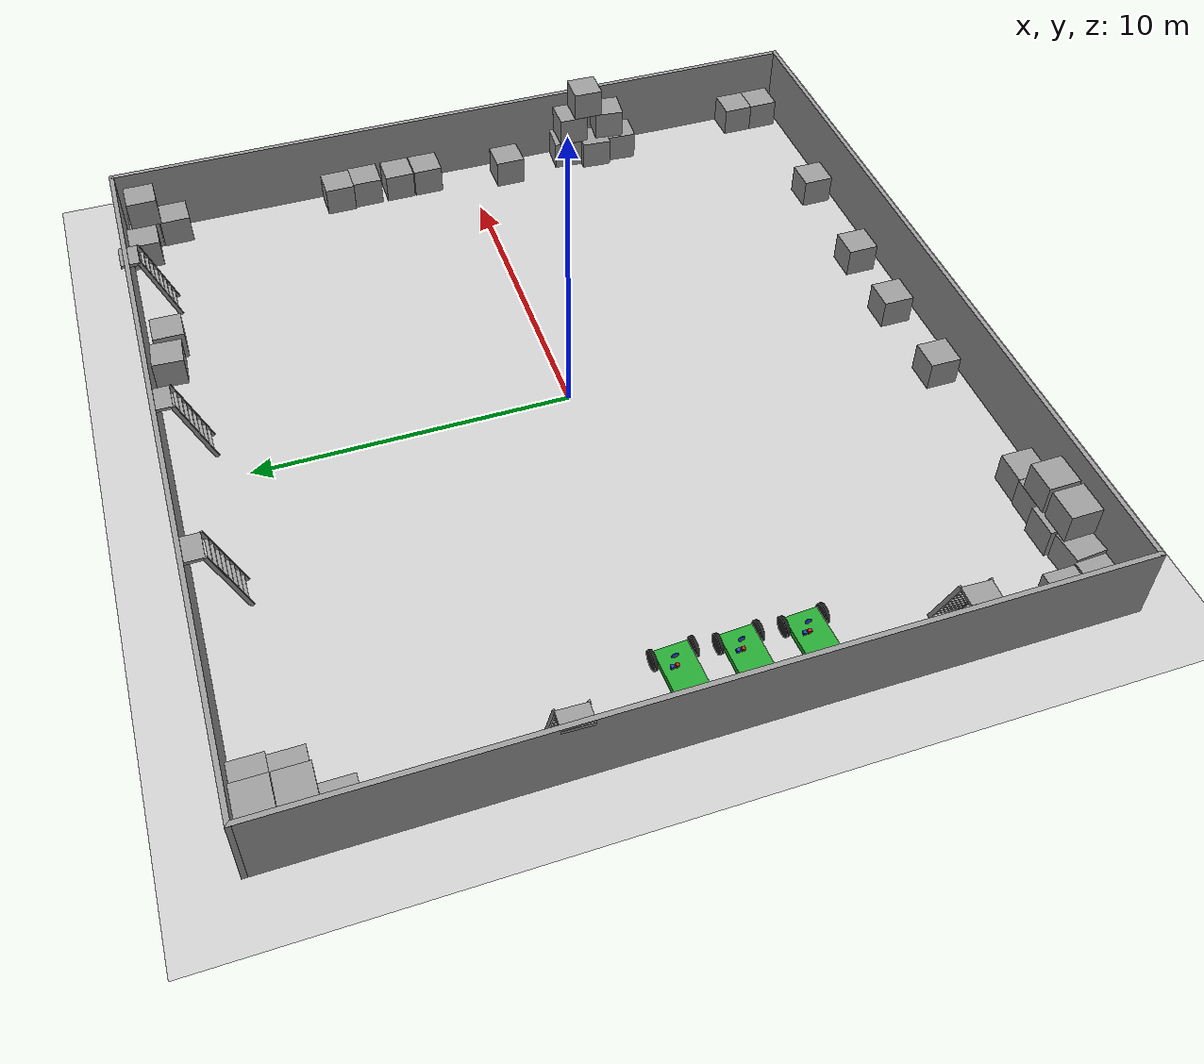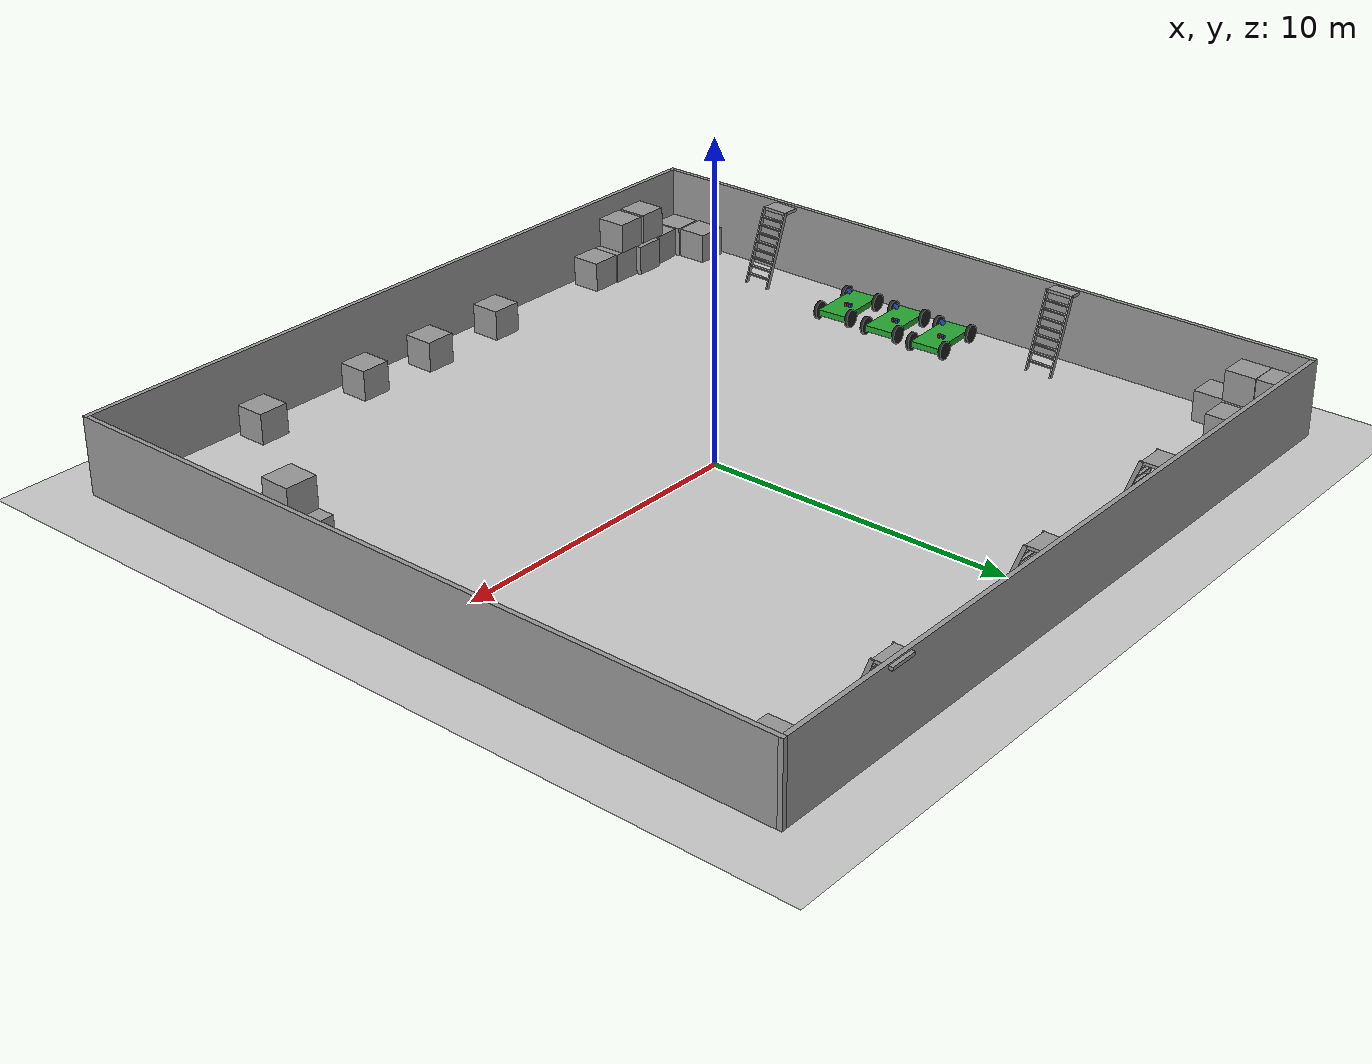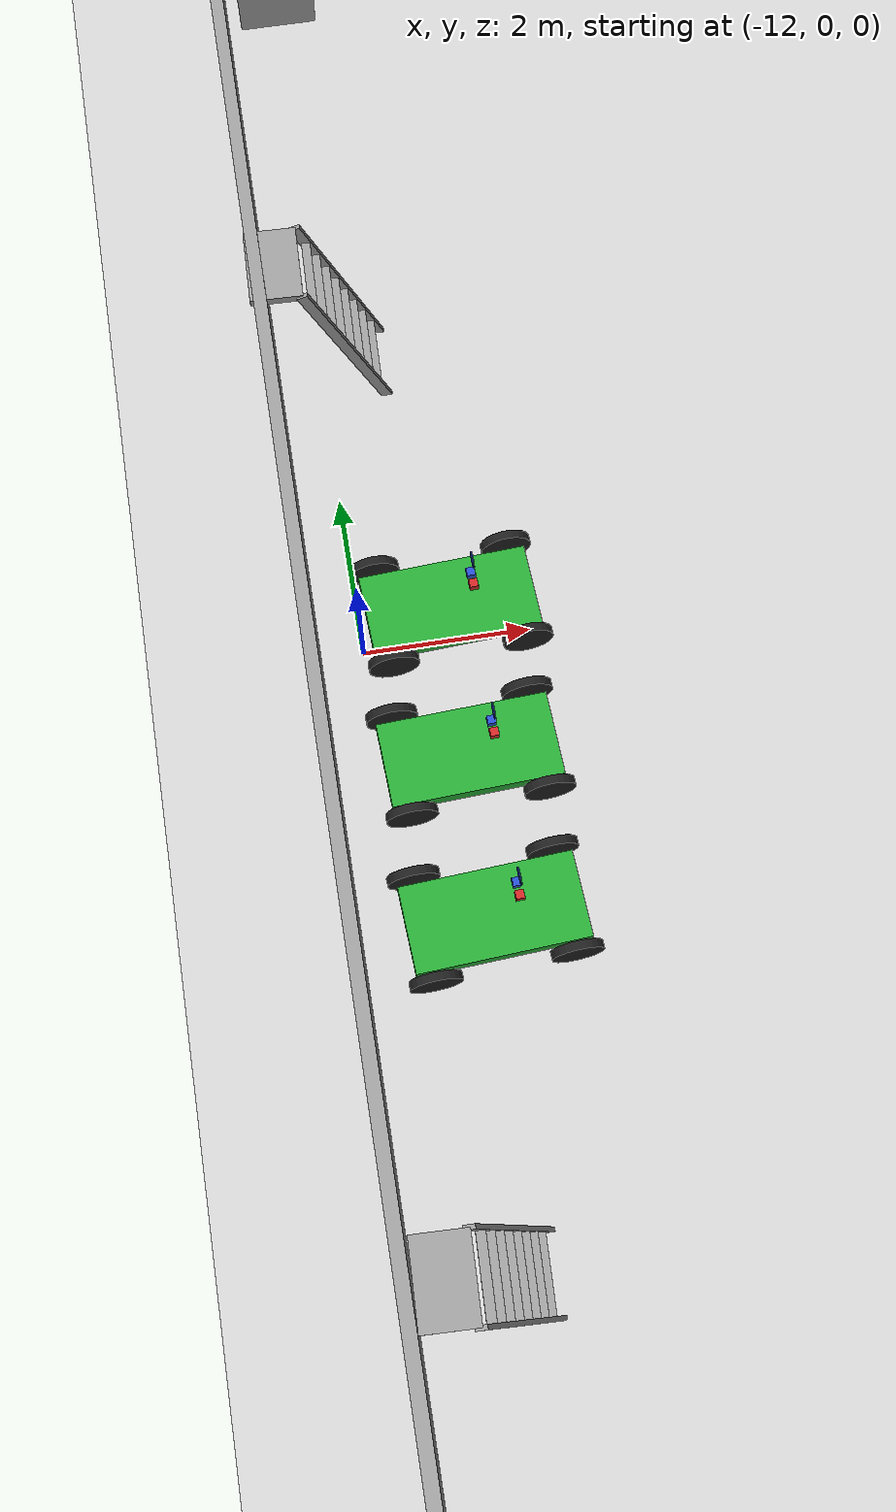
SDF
<sdf version="1.7">
 <world name="default">
  <light name="sun" type="directional">
   <pose>0 0 10 0 -0 0</pose>
   <diffuse>0.8 0.8 0.8 1</diffuse>
   <specular>0.2 0.2 0.2 1</specular>
   <attenuation>
    <range>1000</range>
    <constant>0.9</constant>
    <linear>0.01</linear>
    <quadratic>0.001</quadratic>
   </attenuation>
   <direction>-0.5 0.1 -0.9</direction>
   <spot><inner_angle>0</inner_angle><outer_angle>0</outer_angle><falloff>0</falloff></spot>
  </light>
  <model name="ground_plane">
   <static>1</static>
   <link name="link">
    <collision name="collision">
     <geometry><plane><normal>0 0 1</normal><size>100 100</size></plane></geometry>
     <surface>
      <contact><collide_bitmask>65535</collide_bitmask></contact>
      <friction><ode><mu>100</mu><mu2>50</mu2></ode></friction>
     </surface>
    </collision>
    <visual name="visual">
     <cast_shadows>0</cast_shadows>
     <geometry><plane><normal>0 0 1</normal><size>100 100</size></plane></geometry>
     <material>
      <script><uri>file://media/materials/scripts/gazebo.material</uri><name>Gazebo/Grey</name></script>
     </material>
    </visual>
   </link>
  </model>
  <gravity>0 0 -9.8</gravity>
  <magnetic_field>6e-06 2.3e-05 -4.2e-05</magnetic_field>
  <atmosphere type="adiabatic"/>
  <physics type="ode">
   <max_step_size>0.001</max_step_size>
   <real_time_factor>1</real_time_factor>
   <real_time_update_rate>1000</real_time_update_rate>
  </physics>
  <scene><ambient>0.4 0.4 0.4 1</ambient><background>0.7 0.7 0.7 1</background><shadows>1</shadows></scene>
  <spherical_coordinates>
   <surface_model>EARTH_WGS84</surface_model>
   <latitude_deg>0</latitude_deg>
   <longitude_deg>0</longitude_deg>
   <elevation>0</elevation>
   <heading_deg>0</heading_deg>
  </spherical_coordinates>
  <model name="unit_box">
   <pose>-10.5484 11.7008 0.5 0 0 -0.000958</pose>
   <link name="link">
    <inertial>
     <mass>1</mass>
     <inertia>
      <ixx>0.166667</ixx>
      <ixy>0</ixy>
      <ixz>0</ixz>
      <iyy>0.166667</iyy>
      <iyz>0</iyz>
      <izz>0.166667</izz>
     </inertia>
    </inertial>
    <collision name="collision"><geometry><box><size>1 1 1</size></box></geometry></collision>
    <visual name="visual">
     <geometry><box><size>1 1 1</size></box></geometry>
     <material>
      <script><name>Gazebo/Grey</name><uri>file://media/materials/scripts/gazebo.material</uri></script>
     </material>
    </visual>
   </link>
  </model>
  <model name="unit_box_0">
   <pose>-10.6609 10.7009 0.5 0 0 -0.001123</pose>
   <link name="link">
    <inertial>
     <mass>1</mass>
     <inertia>
      <ixx>0.166667</ixx>
      <ixy>0</ixy>
      <ixz>0</ixz>
      <iyy>0.166667</iyy>
      <iyz>0</iyz>
      <izz>0.166667</izz>
     </inertia>
    </inertial>
    <collision name="collision"><geometry><box><size>1 1 1</size></box></geometry></collision>
    <visual name="visual">
     <geometry><box><size>1 1 1</size></box></geometry>
     <material>
      <script><name>Gazebo/Grey</name><uri>file://media/materials/scripts/gazebo.material</uri></script>
     </material>
    </visual>
   </link>
  </model>
  <model name="unit_box_2">
   <pose>-11.7892 11.6788 0.499993 -4e-06 -1.4e-05 -0.003827</pose>
   <link name="link">
    <inertial>
     <mass>1</mass>
     <inertia>
      <ixx>0.166667</ixx>
      <ixy>0</ixy>
      <ixz>0</ixz>
      <iyy>0.166667</iyy>
      <iyz>0</iyz>
      <izz>0.166667</izz>
     </inertia>
    </inertial>
    <collision name="collision"><geometry><box><size>1 1 1</size></box></geometry></collision>
    <visual name="visual">
     <geometry><box><size>1 1 1</size></box></geometry>
     <material>
      <script><name>Gazebo/Grey</name><uri>file://media/materials/scripts/gazebo.material</uri></script>
     </material>
    </visual>
   </link>
  </model>
  <model name="unit_box_3">
   <pose>-11.7604 11.6669 1.49999 -3.14159 1.1e-05 3.13898</pose>
   <link name="link">
    <inertial>
     <mass>1</mass>
     <inertia>
      <ixx>0.166667</ixx>
      <ixy>0</ixy>
      <ixz>0</ixz>
      <iyy>0.166667</iyy>
      <iyz>0</iyz>
      <izz>0.166667</izz>
     </inertia>
    </inertial>
    <collision name="collision"><geometry><box><size>1 1 1</size></box></geometry></collision>
    <visual name="visual">
     <geometry><box><size>1 1 1</size></box></geometry>
     <material>
      <script><name>Gazebo/Grey</name><uri>file://media/materials/scripts/gazebo.material</uri></script>
     </material>
    </visual>
   </link>
  </model>
  <model name="unit_box_4">
   <pose>-11.8313 9.67825 0.499997 -0 -5e-06 -0.002564</pose>
   <link name="link">
    <inertial>
     <mass>1</mass>
     <inertia>
      <ixx>0.166667</ixx>
      <ixy>0</ixy>
      <ixz>0</ixz>
      <iyy>0.166667</iyy>
      <iyz>0</iyz>
      <izz>0.166667</izz>
     </inertia>
    </inertial>
    <collision name="collision"><geometry><box><size>1 1 1</size></box></geometry></collision>
    <visual name="visual">
     <geometry><box><size>1 1 1</size></box></geometry>
     <material>
      <script><name>Gazebo/Grey</name><uri>file://media/materials/scripts/gazebo.material</uri></script>
     </material>
    </visual>
   </link>
  </model>
  <model name="unit_box_5">
   <pose>-11.7631 10.651 1.5 -3.14159 -0 -0.00395</pose>
   <link name="link">
    <inertial>
     <mass>1</mass>
     <inertia>
      <ixx>0.166667</ixx>
      <ixy>0</ixy>
      <ixz>0</ixz>
      <iyy>0.166667</iyy>
      <iyz>0</iyz>
      <izz>0.166667</izz>
     </inertia>
    </inertial>
    <collision name="collision"><geometry><box><size>1 1 1</size></box></geometry></collision>
    <visual name="visual">
     <geometry><box><size>1 1 1</size></box></geometry>
     <material>
      <script><name>Gazebo/Grey</name><uri>file://media/materials/scripts/gazebo.material</uri></script>
     </material>
    </visual>
   </link>
  </model>
  <model name="unit_box_6">
   <pose>-11.6633 10.6778 0.5 2e-06 -4e-06 -0.002571</pose>
   <link name="link">
    <inertial>
     <mass>1</mass>
     <inertia>
      <ixx>0.166667</ixx>
      <ixy>0</ixy>
      <ixz>0</ixz>
      <iyy>0.166667</iyy>
      <iyz>0</iyz>
      <izz>0.166667</izz>
     </inertia>
    </inertial>
    <collision name="collision"><geometry><box><size>1 1 1</size></box></geometry></collision>
    <visual name="visual">
     <geometry><box><size>1 1 1</size></box></geometry>
     <material>
      <script><name>Gazebo/Grey</name><uri>file://media/materials/scripts/gazebo.material</uri></script>
     </material>
    </visual>
   </link>
  </model>
  <model name="unit_box_10">
   <pose>11.9384 10.5607 0.499988 5e-06 -0 0.018642</pose>
   <link name="link">
    <inertial>
     <mass>1</mass>
     <inertia>
      <ixx>0.166667</ixx>
      <ixy>0</ixy>
      <ixz>0</ixz>
      <iyy>0.166667</iyy>
      <iyz>0</iyz>
      <izz>0.166667</izz>
     </inertia>
    </inertial>
    <collision name="collision"><geometry><box><size>1 1 1</size></box></geometry></collision>
    <visual name="visual">
     <geometry><box><size>1 1 1</size></box></geometry>
     <material>
      <script><name>Gazebo/Grey</name><uri>file://media/materials/scripts/gazebo.material</uri></script>
     </material>
    </visual>
   </link>
  </model>
  <model name="unit_box_11">
   <pose>11.9467 11.5733 0.5 -1e-06 -1e-06 -0.000905</pose>
   <link name="link">
    <inertial>
     <mass>1</mass>
     <inertia>
      <ixx>0.166667</ixx>
      <ixy>0</ixy>
      <ixz>0</ixz>
      <iyy>0.166667</iyy>
      <iyz>0</iyz>
      <izz>0.166667</izz>
     </inertia>
    </inertial>
    <collision name="collision"><geometry><box><size>1 1 1</size></box></geometry></collision>
    <visual name="visual">
     <geometry><box><size>1 1 1</size></box></geometry>
     <material>
      <script><name>Gazebo/Grey</name><uri>file://media/materials/scripts/gazebo.material</uri></script>
     </material>
    </visual>
   </link>
  </model>
  <model name="unit_box_12">
   <pose>10.9468 11.7034 0.499988 5e-06 0 -0.000905</pose>
   <link name="link">
    <inertial>
     <mass>1</mass>
     <inertia>
      <ixx>0.166667</ixx>
      <ixy>0</ixy>
      <ixz>0</ixz>
      <iyy>0.166667</iyy>
      <iyz>0</iyz>
      <izz>0.166667</izz>
     </inertia>
    </inertial>
    <collision name="collision"><geometry><box><size>1 1 1</size></box></geometry></collision>
    <visual name="visual">
     <geometry><box><size>1 1 1</size></box></geometry>
     <material>
      <script><name>Gazebo/Grey</name><uri>file://media/materials/scripts/gazebo.material</uri></script>
     </material>
    </visual>
   </link>
  </model>
  <model name="unit_box_13">
   <pose>11.9323 11.5076 1.49999 4e-06 1.5e-05 0.004138</pose>
   <link name="link">
    <inertial>
     <mass>1</mass>
     <inertia>
      <ixx>0.166667</ixx>
      <ixy>0</ixy>
      <ixz>0</ixz>
      <iyy>0.166667</iyy>
      <iyz>0</iyz>
      <izz>0.166667</izz>
     </inertia>
    </inertial>
    <collision name="collision"><geometry><box><size>1 1 1</size></box></geometry></collision>
    <visual name="visual">
     <geometry><box><size>1 1 1</size></box></geometry>
     <material>
      <script><name>Gazebo/Grey</name><uri>file://media/materials/scripts/gazebo.material</uri></script>
     </material>
    </visual>
   </link>
  </model>
  <model name="unit_box_15">
   <pose>11.9479 1.5494 0.499995 0 1e-05 1.7e-05</pose>
   <link name="link">
    <inertial>
     <mass>1</mass>
     <inertia>
      <ixx>0.166667</ixx>
      <ixy>0</ixy>
      <ixz>0</ixz>
      <iyy>0.166667</iyy>
      <iyz>0</iyz>
      <izz>0.166667</izz>
     </inertia>
    </inertial>
    <collision name="collision"><geometry><box><size>1 1 1</size></box></geometry></collision>
    <visual name="visual">
     <geometry><box><size>1 1 1</size></box></geometry>
     <material>
      <script><name>Gazebo/Grey</name><uri>file://media/materials/scripts/gazebo.material</uri></script>
     </material>
    </visual>
   </link>
  </model>
  <model name="unit_box_16">
   <pose>-10.6579 -11.5048 0.499862 5e-06 -1.3e-05 0.079785</pose>
   <link name="link">
    <inertial>
     <mass>1</mass>
     <inertia>
      <ixx>0.166667</ixx>
      <ixy>0</ixy>
      <ixz>0</ixz>
      <iyy>0.166667</iyy>
      <iyz>0</iyz>
      <izz>0.166667</izz>
     </inertia>
    </inertial>
    <collision name="collision"><geometry><box><size>1 1 1</size></box></geometry></collision>
    <visual name="visual">
     <geometry><box><size>1 1 1</size></box></geometry>
     <material>
      <script><name>Gazebo/Grey</name><uri>file://media/materials/scripts/gazebo.material</uri></script>
     </material>
    </visual>
   </link>
  </model>
  <model name="unit_box_17">
   <pose>-9.98977 -11.5435 1.49988 6e-06 -3e-05 0.011934</pose>
   <link name="link">
    <inertial>
     <mass>1</mass>
     <inertia>
      <ixx>0.166667</ixx>
      <ixy>0</ixy>
      <ixz>0</ixz>
      <iyy>0.166667</iyy>
      <iyz>0</iyz>
      <izz>0.166667</izz>
     </inertia>
    </inertial>
    <collision name="collision"><geometry><box><size>1 1 1</size></box></geometry></collision>
    <visual name="visual">
     <geometry><box><size>1 1 1</size></box></geometry>
     <material>
      <script><name>Gazebo/Grey</name><uri>file://media/materials/scripts/gazebo.material</uri></script>
     </material>
    </visual>
   </link>
  </model>
  <model name="unit_box_17_clone">
   <pose>-8.62537 -11.5193 0.5 -1e-06 1e-06 0.010227</pose>
   <link name="link">
    <inertial>
     <mass>1</mass>
     <inertia>
      <ixx>0.166667</ixx>
      <ixy>0</ixy>
      <ixz>0</ixz>
      <iyy>0.166667</iyy>
      <iyz>0</iyz>
      <izz>0.166667</izz>
     </inertia>
    </inertial>
    <collision name="collision"><geometry><box><size>1 1 1</size></box></geometry></collision>
    <visual name="visual">
     <geometry><box><size>1 1 1</size></box></geometry>
     <material>
      <script><name>Gazebo/Grey</name><uri>file://media/materials/scripts/gazebo.material</uri></script>
     </material>
    </visual>
   </link>
  </model>
  <model name="unit_box_17_clone_0">
   <pose>-11.7955 -10.3916 0.499995 -0 -1e-05 -0.000262</pose>
   <link name="link">
    <inertial>
     <mass>1</mass>
     <inertia>
      <ixx>0.166667</ixx>
      <ixy>0</ixy>
      <ixz>0</ixz>
      <iyy>0.166667</iyy>
      <iyz>0</iyz>
      <izz>0.166667</izz>
     </inertia>
    </inertial>
    <collision name="collision"><geometry><box><size>1 1 1</size></box></geometry></collision>
    <visual name="visual">
     <geometry><box><size>1 1 1</size></box></geometry>
     <material>
      <script><name>Gazebo/Grey</name><uri>file://media/materials/scripts/gazebo.material</uri></script>
     </material>
    </visual>
   </link>
  </model>
  <model name="unit_box_17_clone_1">
   <pose>-11.7294 -11.4535 0.499995 1.57079 -0 0.040552</pose>
   <link name="link">
    <inertial>
     <mass>1</mass>
     <inertia>
      <ixx>0.166667</ixx>
      <ixy>0</ixy>
      <ixz>0</ixz>
      <iyy>0.166667</iyy>
      <iyz>0</iyz>
      <izz>0.166667</izz>
     </inertia>
    </inertial>
    <collision name="collision"><geometry><box><size>1 1 1</size></box></geometry></collision>
    <visual name="visual">
     <geometry><box><size>1 1 1</size></box></geometry>
     <material>
      <script><name>Gazebo/Grey</name><uri>file://media/materials/scripts/gazebo.material</uri></script>
     </material>
    </visual>
   </link>
  </model>
  <model name="unit_box_17_clone_2">
   <pose>-8.88611 -11.5168 1.5 -1e-06 1.9e-05 0.016055</pose>
   <link name="link">
    <inertial>
     <mass>1</mass>
     <inertia>
      <ixx>0.166667</ixx>
      <ixy>0</ixy>
      <ixz>0</ixz>
      <iyy>0.166667</iyy>
      <iyz>0</iyz>
      <izz>0.166667</izz>
     </inertia>
    </inertial>
    <collision name="collision"><geometry><box><size>1 1 1</size></box></geometry></collision>
    <visual name="visual">
     <geometry><box><size>1 1 1</size></box></geometry>
     <material>
      <script><name>Gazebo/Grey</name><uri>file://media/materials/scripts/gazebo.material</uri></script>
     </material>
    </visual>
   </link>
  </model>
  <model name="unit_box_18">
   <pose>11.5985 -4.78924 0.499999 -7e-06 6e-06 -0.070347</pose>
   <link name="link">
    <inertial>
     <mass>1</mass>
     <inertia>
      <ixx>0.166667</ixx>
      <ixy>0</ixy>
      <ixz>0</ixz>
      <iyy>0.166667</iyy>
      <iyz>0</iyz>
      <izz>0.166667</izz>
     </inertia>
    </inertial>
    <collision name="collision"><geometry><box><size>1 1 1</size></box></geometry></collision>
    <visual name="visual">
     <geometry><box><size>1 1 1</size></box></geometry>
     <material>
      <script><name>Gazebo/Grey</name><uri>file://media/materials/scripts/gazebo.material</uri></script>
     </material>
    </visual>
   </link>
  </model>
  <model name="unit_box_19">
   <pose>11.9085 -3.80861 0.5 0 1e-06 -0.070342</pose>
   <link name="link">
    <inertial>
     <mass>1</mass>
     <inertia>
      <ixx>0.166667</ixx>
      <ixy>0</ixy>
      <ixz>0</ixz>
      <iyy>0.166667</iyy>
      <iyz>0</iyz>
      <izz>0.166667</izz>
     </inertia>
    </inertial>
    <collision name="collision"><geometry><box><size>1 1 1</size></box></geometry></collision>
    <visual name="visual">
     <geometry><box><size>1 1 1</size></box></geometry>
     <material>
      <script><name>Gazebo/Grey</name><uri>file://media/materials/scripts/gazebo.material</uri></script>
     </material>
    </visual>
   </link>
  </model>
  <model name="unit_box_20">
   <pose>11.7268 -5.80078 0.5 7e-06 7e-06 -0.070359</pose>
   <link name="link">
    <inertial>
     <mass>1</mass>
     <inertia>
      <ixx>0.166667</ixx>
      <ixy>0</ixy>
      <ixz>0</ixz>
      <iyy>0.166667</iyy>
      <iyz>0</iyz>
      <izz>0.166667</izz>
     </inertia>
    </inertial>
    <collision name="collision"><geometry><box><size>1 1 1</size></box></geometry></collision>
    <visual name="visual">
     <geometry><box><size>1 1 1</size></box></geometry>
     <material>
      <script><name>Gazebo/Grey</name><uri>file://media/materials/scripts/gazebo.material</uri></script>
     </material>
    </visual>
   </link>
  </model>
  <model name="unit_box_20_clone">
   <pose>7.00934 -11.5415 0.499995 0 1e-05 0.002791</pose>
   <link name="link">
    <inertial>
     <mass>1</mass>
     <inertia>
      <ixx>0.166667</ixx>
      <ixy>0</ixy>
      <ixz>0</ixz>
      <iyy>0.166667</iyy>
      <iyz>0</iyz>
      <izz>0.166667</izz>
     </inertia>
    </inertial>
    <collision name="collision"><geometry><box><size>1 1 1</size></box></geometry></collision>
    <visual name="visual">
     <geometry><box><size>1 1 1</size></box></geometry>
     <material>
      <script><name>Gazebo/Grey</name><uri>file://media/materials/scripts/gazebo.material</uri></script>
     </material>
    </visual>
   </link>
  </model>
  <model name="unit_box_20_clone_0">
   <pose>11.8643 -5.36609 1.5 -5e-06 1e-05 -0.111309</pose>
   <link name="link">
    <inertial>
     <mass>1</mass>
     <inertia>
      <ixx>0.166667</ixx>
      <ixy>0</ixy>
      <ixz>0</ixz>
      <iyy>0.166667</iyy>
      <iyz>0</iyz>
      <izz>0.166667</izz>
     </inertia>
    </inertial>
    <collision name="collision"><geometry><box><size>1 1 1</size></box></geometry></collision>
    <visual name="visual">
     <geometry><box><size>1 1 1</size></box></geometry>
     <material>
      <script><name>Gazebo/Grey</name><uri>file://media/materials/scripts/gazebo.material</uri></script>
     </material>
    </visual>
   </link>
  </model>
  <model name="unit_box_20_clone_1">
   <pose>11.9239 -4.53395 2.5 4e-06 1.9e-05 -0.02535</pose>
   <link name="link">
    <inertial>
     <mass>1</mass>
     <inertia>
      <ixx>0.166667</ixx>
      <ixy>0</ixy>
      <ixz>0</ixz>
      <iyy>0.166667</iyy>
      <iyz>0</iyz>
      <izz>0.166667</izz>
     </inertia>
    </inertial>
    <collision name="collision"><geometry><box><size>1 1 1</size></box></geometry></collision>
    <visual name="visual">
     <geometry><box><size>1 1 1</size></box></geometry>
     <material>
      <script><name>Gazebo/Grey</name><uri>file://media/materials/scripts/gazebo.material</uri></script>
     </material>
    </visual>
   </link>
  </model>
  <model name="unit_box_21">
   <pose>11.9159 -3.98319 1.5 4e-06 6e-06 -0.010982</pose>
   <link name="link">
    <inertial>
     <mass>1</mass>
     <inertia>
      <ixx>0.166667</ixx>
      <ixy>0</ixy>
      <ixz>0</ixz>
      <iyy>0.166667</iyy>
      <iyz>0</iyz>
      <izz>0.166667</izz>
     </inertia>
    </inertial>
    <collision name="collision"><geometry><box><size>1 1 1</size></box></geometry></collision>
    <visual name="visual">
     <geometry><box><size>1 1 1</size></box></geometry>
     <material>
      <script><name>Gazebo/Grey</name><uri>file://media/materials/scripts/gazebo.material</uri></script>
     </material>
    </visual>
   </link>
  </model>
  <model name="unit_box_22">
   <pose>11.9475 -11.539 0.499995 0 1e-05 0.00075</pose>
   <link name="link">
    <inertial>
     <mass>1</mass>
     <inertia>
      <ixx>0.166667</ixx>
      <ixy>0</ixy>
      <ixz>0</ixz>
      <iyy>0.166667</iyy>
      <iyz>0</iyz>
      <izz>0.166667</izz>
     </inertia>
    </inertial>
    <collision name="collision"><geometry><box><size>1 1 1</size></box></geometry></collision>
    <visual name="visual">
     <geometry><box><size>1 1 1</size></box></geometry>
     <material>
      <script><name>Gazebo/Grey</name><uri>file://media/materials/scripts/gazebo.material</uri></script>
     </material>
    </visual>
   </link>
  </model>
  <model name="unit_box_23">
   <pose>6.13032 11.5243 0.499995 1e-05 -0 -0.007274</pose>
   <link name="link">
    <inertial>
     <mass>1</mass>
     <inertia>
      <ixx>0.166667</ixx>
      <ixy>0</ixy>
      <ixz>0</ixz>
      <iyy>0.166667</iyy>
      <iyz>0</iyz>
      <izz>0.166667</izz>
     </inertia>
    </inertial>
    <collision name="collision"><geometry><box><size>1 1 1</size></box></geometry></collision>
    <visual name="visual">
     <geometry><box><size>1 1 1</size></box></geometry>
     <material>
      <script><name>Gazebo/Grey</name><uri>file://media/materials/scripts/gazebo.material</uri></script>
     </material>
    </visual>
   </link>
  </model>
  <model name="unit_box_24">
   <pose>4.94336 11.6796 0.499995 -1.57081 -1.57079 1.51865</pose>
   <link name="link">
    <inertial>
     <mass>1</mass>
     <inertia>
      <ixx>0.166667</ixx>
      <ixy>0</ixy>
      <ixz>0</ixz>
      <iyy>0.166667</iyy>
      <iyz>0</iyz>
      <izz>0.166667</izz>
     </inertia>
    </inertial>
    <collision name="collision"><geometry><box><size>1 1 1</size></box></geometry></collision>
    <visual name="visual">
     <geometry><box><size>1 1 1</size></box></geometry>
     <material>
      <script><name>Gazebo/Grey</name><uri>file://media/materials/scripts/gazebo.material</uri></script>
     </material>
    </visual>
   </link>
  </model>
  <model name="unit_box_25">
   <pose>11.9479 2.5813 0.499995 0 1e-05 1.6e-05</pose>
   <link name="link">
    <inertial>
     <mass>1</mass>
     <inertia>
      <ixx>0.166667</ixx>
      <ixy>0</ixy>
      <ixz>0</ixz>
      <iyy>0.166667</iyy>
      <iyz>0</iyz>
      <izz>0.166667</izz>
     </inertia>
    </inertial>
    <collision name="collision"><geometry><box><size>1 1 1</size></box></geometry></collision>
    <visual name="visual">
     <geometry><box><size>1 1 1</size></box></geometry>
     <material>
      <script><name>Gazebo/Grey</name><uri>file://media/materials/scripts/gazebo.material</uri></script>
     </material>
    </visual>
   </link>
  </model>
  <model name="unit_box_26">
   <pose>11.9477 3.76706 0.499995 -1e-05 -0 0.000301</pose>
   <link name="link">
    <inertial>
     <mass>1</mass>
     <inertia>
      <ixx>0.166667</ixx>
      <ixy>0</ixy>
      <ixz>0</ixz>
      <iyy>0.166667</iyy>
      <iyz>0</iyz>
      <izz>0.166667</izz>
     </inertia>
    </inertial>
    <collision name="collision"><geometry><box><size>1 1 1</size></box></geometry></collision>
    <visual name="visual">
     <geometry><box><size>1 1 1</size></box></geometry>
     <material>
      <script><name>Gazebo/Grey</name><uri>file://media/materials/scripts/gazebo.material</uri></script>
     </material>
    </visual>
   </link>
  </model>
  <model name="unit_box_27">
   <pose>11.8814 4.76704 0.499995 -1e-05 0 0.000302</pose>
   <link name="link">
    <inertial>
     <mass>1</mass>
     <inertia>
      <ixx>0.166667</ixx>
      <ixy>0</ixy>
      <ixz>0</ixz>
      <iyy>0.166667</iyy>
      <iyz>0</iyz>
      <izz>0.166667</izz>
     </inertia>
    </inertial>
    <collision name="collision"><geometry><box><size>1 1 1</size></box></geometry></collision>
    <visual name="visual">
     <geometry><box><size>1 1 1</size></box></geometry>
     <material>
      <script><name>Gazebo/Grey</name><uri>file://media/materials/scripts/gazebo.material</uri></script>
     </material>
    </visual>
   </link>
  </model>
  <model name="unit_box_28">
   <pose>-7.61872 -11.5424 0.499995 -1e-05 -0 0.003873</pose>
   <link name="link">
    <inertial>
     <mass>1</mass>
     <inertia>
      <ixx>0.166667</ixx>
      <ixy>0</ixy>
      <ixz>0</ixz>
      <iyy>0.166667</iyy>
      <iyz>0</iyz>
      <izz>0.166667</izz>
     </inertia>
    </inertial>
    <collision name="collision"><geometry><box><size>1 1 1</size></box></geometry></collision>
    <visual name="visual">
     <geometry><box><size>1 1 1</size></box></geometry>
     <material>
      <script><name>Gazebo/Grey</name><uri>file://media/materials/scripts/gazebo.material</uri></script>
     </material>
    </visual>
   </link>
  </model>
  <model name="unit_box_29">
   <pose>-2.65126 -11.3902 0.5 0 -0 0</pose>
   <link name="link">
    <inertial>
     <mass>1</mass>
     <inertia>
      <ixx>0.166667</ixx>
      <ixy>0</ixy>
      <ixz>0</ixz>
      <iyy>0.166667</iyy>
      <iyz>0</iyz>
      <izz>0.166667</izz>
     </inertia>
    </inertial>
    <collision name="collision"><geometry><box><size>1 1 1</size></box></geometry></collision>
    <visual name="visual">
     <geometry><box><size>1 1 1</size></box></geometry>
     <material>
      <script><name>Gazebo/Grey</name><uri>file://media/materials/scripts/gazebo.material</uri></script>
     </material>
    </visual>
   </link>
  </model>
  <model name="unit_box_30">
   <pose>3.08895 -11.3753 0.499995 -1e-05 -0 -1.1e-05</pose>
   <link name="link">
    <inertial>
     <mass>1</mass>
     <inertia>
      <ixx>0.166667</ixx>
      <ixy>0</ixy>
      <ixz>0</ixz>
      <iyy>0.166667</iyy>
      <iyz>0</iyz>
      <izz>0.166667</izz>
     </inertia>
    </inertial>
    <collision name="collision"><geometry><box><size>1 1 1</size></box></geometry></collision>
    <visual name="visual">
     <geometry><box><size>1 1 1</size></box></geometry>
     <material>
      <script><name>Gazebo/Grey</name><uri>file://media/materials/scripts/gazebo.material</uri></script>
     </material>
    </visual>
   </link>
  </model>
  <model name="unit_box_31">
   <pose>0.379472 -11.3219 0.499995 1e-05 -0 0</pose>
   <link name="link">
    <inertial>
     <mass>1</mass>
     <inertia>
      <ixx>0.166667</ixx>
      <ixy>0</ixy>
      <ixz>0</ixz>
      <iyy>0.166667</iyy>
      <iyz>0</iyz>
      <izz>0.166667</izz>
     </inertia>
    </inertial>
    <collision name="collision"><geometry><box><size>1 1 1</size></box></geometry></collision>
    <visual name="visual">
     <geometry><box><size>1 1 1</size></box></geometry>
     <material>
      <script><name>Gazebo/Grey</name><uri>file://media/materials/scripts/gazebo.material</uri></script>
     </material>
    </visual>
   </link>
  </model>
  <model name="unit_box_32">
   <pose>11.5214 -1.4211 0.499995 0 -1e-05 2e-06</pose>
   <link name="link">
    <inertial>
     <mass>1</mass>
     <inertia>
      <ixx>0.166667</ixx>
      <ixy>0</ixy>
      <ixz>0</ixz>
      <iyy>0.166667</iyy>
      <iyz>0</iyz>
      <izz>0.166667</izz>
     </inertia>
    </inertial>
    <collision name="collision"><geometry><box><size>1 1 1</size></box></geometry></collision>
    <visual name="visual">
     <geometry><box><size>1 1 1</size></box></geometry>
     <material>
      <script><name>Gazebo/Grey</name><uri>file://media/materials/scripts/gazebo.material</uri></script>
     </material>
    </visual>
   </link>
  </model>
  <model name="unit_box_33">
   <pose>11.9475 -10.539 0.499995 -0 1e-05 0.000745</pose>
   <link name="link">
    <inertial>
     <mass>1</mass>
     <inertia>
      <ixx>0.166667</ixx>
      <ixy>0</ixy>
      <ixz>0</ixz>
      <iyy>0.166667</iyy>
      <iyz>0</iyz>
      <izz>0.166667</izz>
     </inertia>
    </inertial>
    <collision name="collision"><geometry><box><size>1 1 1</size></box></geometry></collision>
    <visual name="visual">
     <geometry><box><size>1 1 1</size></box></geometry>
     <material>
      <script><name>Gazebo/Grey</name><uri>file://media/materials/scripts/gazebo.material</uri></script>
     </material>
    </visual>
   </link>
  </model>
  <model name="ladder_70deg_0rails">
   <static>1</static>
   <link name="step0">
    <pose>0 0.097059 0.266667 0 -0 0</pose>
    <inertial>
     <mass>9.75482</mass>
     <inertia>
      <ixx>0.00957124</ixx>
      <iyy>0.65963</iyy>
      <izz>0.666842</izz>
      <ixy>0</ixy>
      <ixz>0</ixz>
      <iyz>0</iyz>
     </inertia>
    </inertial>
    <collision name="collision"><geometry><box><size>0.9 0.1016 0.0381</size></box></geometry></collision>
    <visual name="visual">
     <geometry><box><size>0.9 0.1016 0.0381</size></box></geometry>
     <material>
      <script><uri>file://media/materials/scripts/gazebo.material</uri><name>Gazebo/Grey</name></script>
     </material>
    </visual>
   </link>
   <link name="step1">
    <pose>0 0.194117 0.533333 0 -0 0</pose>
    <inertial>
     <mass>9.75482</mass>
     <inertia>
      <ixx>0.00957124</ixx>
      <iyy>0.65963</iyy>
      <izz>0.666842</izz>
      <ixy>0</ixy>
      <ixz>0</ixz>
      <iyz>0</iyz>
     </inertia>
    </inertial>
    <collision name="collision"><geometry><box><size>0.9 0.1016 0.0381</size></box></geometry></collision>
    <visual name="visual">
     <geometry><box><size>0.9 0.1016 0.0381</size></box></geometry>
     <material>
      <script><uri>file://media/materials/scripts/gazebo.material</uri><name>Gazebo/Grey</name></script>
     </material>
    </visual>
   </link>
   <link name="step2">
    <pose>0 0.291176 0.8 0 -0 0</pose>
    <inertial>
     <mass>9.75482</mass>
     <inertia>
      <ixx>0.00957124</ixx>
      <iyy>0.65963</iyy>
      <izz>0.666842</izz>
      <ixy>0</ixy>
      <ixz>0</ixz>
      <iyz>0</iyz>
     </inertia>
    </inertial>
    <collision name="collision"><geometry><box><size>0.9 0.1016 0.0381</size></box></geometry></collision>
    <visual name="visual">
     <geometry><box><size>0.9 0.1016 0.0381</size></box></geometry>
     <material>
      <script><uri>file://media/materials/scripts/gazebo.material</uri><name>Gazebo/Grey</name></script>
     </material>
    </visual>
   </link>
   <link name="step3">
    <pose>0 0.388235 1.06667 0 -0 0</pose>
    <inertial>
     <mass>9.75482</mass>
     <inertia>
      <ixx>0.00957124</ixx>
      <iyy>0.65963</iyy>
      <izz>0.666842</izz>
      <ixy>0</ixy>
      <ixz>0</ixz>
      <iyz>0</iyz>
     </inertia>
    </inertial>
    <collision name="collision"><geometry><box><size>0.9 0.1016 0.0381</size></box></geometry></collision>
    <visual name="visual">
     <geometry><box><size>0.9 0.1016 0.0381</size></box></geometry>
     <material>
      <script><uri>file://media/materials/scripts/gazebo.material</uri><name>Gazebo/Grey</name></script>
     </material>
    </visual>
   </link>
   <link name="step4">
    <pose>0 0.485294 1.33333 0 -0 0</pose>
    <inertial>
     <mass>9.75482</mass>
     <inertia>
      <ixx>0.00957124</ixx>
      <iyy>0.65963</iyy>
      <izz>0.666842</izz>
      <ixy>0</ixy>
      <ixz>0</ixz>
      <iyz>0</iyz>
     </inertia>
    </inertial>
    <collision name="collision"><geometry><box><size>0.9 0.1016 0.0381</size></box></geometry></collision>
    <visual name="visual">
     <geometry><box><size>0.9 0.1016 0.0381</size></box></geometry>
     <material>
      <script><uri>file://media/materials/scripts/gazebo.material</uri><name>Gazebo/Grey</name></script>
     </material>
    </visual>
   </link>
   <link name="step5">
    <pose>0 0.582352 1.6 0 -0 0</pose>
    <inertial>
     <mass>9.75482</mass>
     <inertia>
      <ixx>0.00957124</ixx>
      <iyy>0.65963</iyy>
      <izz>0.666842</izz>
      <ixy>0</ixy>
      <ixz>0</ixz>
      <iyz>0</iyz>
     </inertia>
    </inertial>
    <collision name="collision"><geometry><box><size>0.9 0.1016 0.0381</size></box></geometry></collision>
    <visual name="visual">
     <geometry><box><size>0.9 0.1016 0.0381</size></box></geometry>
     <material>
      <script><uri>file://media/materials/scripts/gazebo.material</uri><name>Gazebo/Grey</name></script>
     </material>
    </visual>
   </link>
   <link name="step6">
    <pose>0 0.679411 1.86667 0 -0 0</pose>
    <inertial>
     <mass>9.75482</mass>
     <inertia>
      <ixx>0.00957124</ixx>
      <iyy>0.65963</iyy>
      <izz>0.666842</izz>
      <ixy>0</ixy>
      <ixz>0</ixz>
      <iyz>0</iyz>
     </inertia>
    </inertial>
    <collision name="collision"><geometry><box><size>0.9 0.1016 0.0381</size></box></geometry></collision>
    <visual name="visual">
     <geometry><box><size>0.9 0.1016 0.0381</size></box></geometry>
     <material>
      <script><uri>file://media/materials/scripts/gazebo.material</uri><name>Gazebo/Grey</name></script>
     </material>
    </visual>
   </link>
   <link name="step7">
    <pose>0 0.77647 2.13333 0 -0 0</pose>
    <inertial>
     <mass>9.75482</mass>
     <inertia>
      <ixx>0.00957124</ixx>
      <iyy>0.65963</iyy>
      <izz>0.666842</izz>
      <ixy>0</ixy>
      <ixz>0</ixz>
      <iyz>0</iyz>
     </inertia>
    </inertial>
    <collision name="collision"><geometry><box><size>0.9 0.1016 0.0381</size></box></geometry></collision>
    <visual name="visual">
     <geometry><box><size>0.9 0.1016 0.0381</size></box></geometry>
     <material>
      <script><uri>file://media/materials/scripts/gazebo.material</uri><name>Gazebo/Grey</name></script>
     </material>
    </visual>
   </link>
   <link name="landing">
    <pose>0 1.17353 2.4 0 -0 0</pose>
    <inertial>
     <mass>57.6072</mass>
     <inertia><ixx>1.73518</ixx><iyy>3.89545</iyy><izz>5.6167</izz><ixy>0</ixy><ixz>0</ixz><iyz>0</iyz></inertia>
    </inertial>
    <collision name="collision"><geometry><box><size>0.9 0.6 0.1016</size></box></geometry></collision>
    <visual name="visual">
     <geometry><box><size>0.9 0.6 0.1016</size></box></geometry>
     <material>
      <script><uri>file://media/materials/scripts/gazebo.material</uri><name>Gazebo/Grey</name></script>
     </material>
    </visual>
   </link>
   <link name="left_side_wall">
    <pose>-0.45 0.436764 1.2 1.22173 -0 0</pose>
    <collision name="collision"><geometry><box><size>0.0508 2.63403 0.13</size></box></geometry></collision>
    <visual name="visual">
     <geometry><box><size>0.0508 2.63403 0.13</size></box></geometry>
     <material>
      <script><uri>file://media/materials/scripts/gazebo.material</uri><name>Gazebo/Grey</name></script>
     </material>
    </visual>
   </link>
   <link name="right_side_wall">
    <pose>0.45 0.436764 1.2 1.22173 -0 0</pose>
    <collision name="collision"><geometry><box><size>0.0508 2.63403 0.13</size></box></geometry></collision>
    <visual name="visual">
     <geometry><box><size>0.0508 2.63403 0.13</size></box></geometry>
     <material>
      <script><uri>file://media/materials/scripts/gazebo.material</uri><name>Gazebo/Grey</name></script>
     </material>
    </visual>
   </link>
   <pose>-4.32634 10.7561 0 0 -0 0</pose>
  </model>
  <model name="car">
   <link name="chassis">
    <pose>0 0 0.3 0 -0 0</pose>
    <collision name="collision"><geometry><box><size>2 1 0.2</size></box></geometry></collision>
    <visual name="visual">
     <geometry><box><size>2 1 0.2</size></box></geometry>
     <material>
      <script><uri>file://media/materials/scripts/gazebo.material</uri><name>Gazebo/Green</name></script>
     </material>
    </visual>
    <inertial>
     <inertia><ixx>1</ixx><ixy>0</ixy><ixz>0</ixz><iyy>1</iyy><iyz>0</iyz><izz>1</izz></inertia>
     <mass>1</mass>
    </inertial>
   </link>
   <link name="front_left_wheel">
    <pose>0.8 0.6 0.3 -0 1.5707 1.5707</pose>
    <collision name="collision">
     <geometry><cylinder><radius>0.3</radius><length>0.1</length></cylinder></geometry>
    </collision>
    <visual name="visual">
     <geometry><cylinder><radius>0.3</radius><length>0.1</length></cylinder></geometry>
     <material>
      <script><uri>file://media/materials/scripts/gazebo.material</uri><name>Gazebo/Black</name></script>
     </material>
    </visual>
    <inertial>
     <inertia><ixx>1</ixx><ixy>0</ixy><ixz>0</ixz><iyy>1</iyy><iyz>0</iyz><izz>1</izz></inertia>
     <mass>1</mass>
    </inertial>
   </link>
   <link name="front_right_wheel">
    <pose>0.8 -0.6 0.3 -0 1.5707 1.5707</pose>
    <collision name="collision">
     <geometry><cylinder><radius>0.3</radius><length>0.1</length></cylinder></geometry>
    </collision>
    <visual name="visual">
     <geometry><cylinder><radius>0.3</radius><length>0.1</length></cylinder></geometry>
     <material>
      <script><uri>file://media/materials/scripts/gazebo.material</uri><name>Gazebo/Black</name></script>
     </material>
    </visual>
    <inertial>
     <inertia><ixx>1</ixx><ixy>0</ixy><ixz>0</ixz><iyy>1</iyy><iyz>0</iyz><izz>1</izz></inertia>
     <mass>1</mass>
    </inertial>
   </link>
   <link name="back_right_wheel">
    <pose>-0.8 -0.6 0.3 -0 1.5707 1.5707</pose>
    <collision name="collision">
     <geometry><cylinder><radius>0.3</radius><length>0.1</length></cylinder></geometry>
    </collision>
    <visual name="visual">
     <geometry><cylinder><radius>0.3</radius><length>0.1</length></cylinder></geometry>
     <material>
      <script><uri>file://media/materials/scripts/gazebo.material</uri><name>Gazebo/Black</name></script>
     </material>
    </visual>
    <inertial>
     <inertia><ixx>1</ixx><ixy>0</ixy><ixz>0</ixz><iyy>1</iyy><iyz>0</iyz><izz>1</izz></inertia>
     <mass>1</mass>
    </inertial>
   </link>
   <link name="back_left_wheel">
    <pose>-0.8 0.6 0.3 -0 1.5707 1.5707</pose>
    <collision name="collision">
     <geometry><cylinder><radius>0.3</radius><length>0.1</length></cylinder></geometry>
    </collision>
    <visual name="visual">
     <geometry><cylinder><radius>0.3</radius><length>0.1</length></cylinder></geometry>
     <material>
      <script><uri>file://media/materials/scripts/gazebo.material</uri><name>Gazebo/Black</name></script>
     </material>
    </visual>
    <inertial>
     <inertia><ixx>1</ixx><ixy>0</ixy><ixz>0</ixz><iyy>1</iyy><iyz>0</iyz><izz>1</izz></inertia>
     <mass>1</mass>
    </inertial>
   </link>
   <link name="gas_pedal">
    <pose>0.3 0.1 0.5 0 -0 0</pose>
    <collision name="collision"><geometry><box><size>0.1 0.1 0.1</size></box></geometry></collision>
    <visual name="visual">
     <geometry><box><size>0.1 0.1 0.1</size></box></geometry>
     <material>
      <script><uri>file://media/materials/scripts/gazebo.material</uri><name>Gazebo/Red</name></script>
     </material>
    </visual>
    <inertial>
     <inertia><ixx>1</ixx><ixy>0</ixy><ixz>0</ixz><iyy>1</iyy><iyz>0</iyz><izz>1</izz></inertia>
     <mass>1</mass>
    </inertial>
   </link>
   <link name="brake_pedal">
    <pose>0.3 0.25 0.5 0 -0 0</pose>
    <collision name="collision"><geometry><box><size>0.1 0.1 0.1</size></box></geometry></collision>
    <visual name="visual">
     <geometry><box><size>0.1 0.1 0.1</size></box></geometry>
     <material>
      <script><uri>file://media/materials/scripts/gazebo.material</uri><name>Gazebo/Blue</name></script>
     </material>
    </visual>
    <inertial>
     <inertia><ixx>1</ixx><ixy>0</ixy><ixz>0</ixz><iyy>1</iyy><iyz>0</iyz><izz>1</izz></inertia>
     <mass>1</mass>
    </inertial>
   </link>
   <link name="steering_wheel">
    <pose>0.3 0.2 1 0 1.5707 0</pose>
    <collision name="collision">
     <geometry><cylinder><radius>0.1</radius><length>0.01</length></cylinder></geometry>
    </collision>
    <visual name="visual">
     <geometry><cylinder><radius>0.1</radius><length>0.01</length></cylinder></geometry>
     <material>
      <script><uri>file://media/materials/scripts/gazebo.material</uri><name>Gazebo/Blue</name></script>
     </material>
    </visual>
    <inertial>
     <inertia><ixx>1</ixx><ixy>0</ixy><ixz>0</ixz><iyy>1</iyy><iyz>0</iyz><izz>1</izz></inertia>
     <mass>1</mass>
    </inertial>
   </link>
   <joint name="gas_joint" type="prismatic">
    <parent>chassis</parent>
    <child>gas_pedal</child>
    <axis>
     <xyz expressed_in="__model__">1 0 0</xyz>
     <limit><lower>0</lower><upper>0.2</upper></limit>
     <dynamics><spring_reference>0</spring_reference><spring_stiffness>0</spring_stiffness></dynamics>
    </axis>
   </joint>
   <joint name="brake_joint" type="prismatic">
    <parent>chassis</parent>
    <child>brake_pedal</child>
    <axis>
     <xyz expressed_in="__model__">1 0 0</xyz>
     <limit><lower>0</lower><upper>0.2</upper></limit>
     <dynamics><spring_reference>0</spring_reference><spring_stiffness>0</spring_stiffness></dynamics>
    </axis>
   </joint>
   <joint name="steering_joint" type="revolute">
    <parent>chassis</parent>
    <child>steering_wheel</child>
    <axis>
     <xyz expressed_in="__model__">1 0 0</xyz>
     <limit><lower>-7.853</lower><upper>7.853</upper></limit>
     <dynamics><spring_reference>0</spring_reference><spring_stiffness>0</spring_stiffness></dynamics>
    </axis>
   </joint>
   <joint name="front_left_joint" type="revolute2">
    <parent>chassis</parent>
    <child>front_left_wheel</child>
    <axis>
     <xyz expressed_in="__model__">0 0 1</xyz>
     <limit><lower>-1.5526e-05</lower><upper>-1.5526e-05</upper></limit>
     <dynamics><spring_reference>0</spring_reference><spring_stiffness>0</spring_stiffness></dynamics>
    </axis>
    <axis2>
     <xyz expressed_in="__model__">0 1 0</xyz>
     <limit><upper>1e+16</upper><lower>-1e+16</lower></limit>
     <dynamics><spring_reference>0</spring_reference><spring_stiffness>0</spring_stiffness></dynamics>
    </axis2>
    <physics><ode><limit><cfm>0</cfm><erp>0.9</erp></limit></ode></physics>
   </joint>
   <joint name="front_right_joint" type="revolute2">
    <parent>chassis</parent>
    <child>front_right_wheel</child>
    <axis>
     <xyz expressed_in="__model__">0 0 1</xyz>
     <limit><lower>-1.5526e-05</lower><upper>-1.5526e-05</upper></limit>
     <dynamics><spring_reference>0</spring_reference><spring_stiffness>0</spring_stiffness></dynamics>
    </axis>
    <axis2>
     <xyz expressed_in="__model__">0 1 0</xyz>
     <limit><upper>1e+16</upper><lower>-1e+16</lower></limit>
     <dynamics><spring_reference>0</spring_reference><spring_stiffness>0</spring_stiffness></dynamics>
    </axis2>
    <physics><ode><limit><cfm>0</cfm><erp>0.9</erp></limit></ode></physics>
   </joint>
   <joint name="back_right_joint" type="revolute2">
    <parent>chassis</parent>
    <child>back_right_wheel</child>
    <axis>
     <xyz expressed_in="__model__">0 0 1</xyz>
     <limit><lower>0</lower><upper>0</upper></limit>
     <dynamics><spring_reference>0</spring_reference><spring_stiffness>0</spring_stiffness></dynamics>
    </axis>
    <axis2>
     <xyz expressed_in="__model__">0 1 0</xyz>
     <limit><upper>1e+16</upper><lower>-1e+16</lower></limit>
     <dynamics><spring_reference>0</spring_reference><spring_stiffness>0</spring_stiffness></dynamics>
    </axis2>
    <physics><ode><limit><cfm>0</cfm><erp>0.9</erp></limit></ode></physics>
   </joint>
   <joint name="back_left_joint" type="revolute2">
    <parent>chassis</parent>
    <child>back_left_wheel</child>
    <axis>
     <xyz expressed_in="__model__">0 0 1</xyz>
     <limit><lower>0</lower><upper>0</upper></limit>
     <dynamics><spring_reference>0</spring_reference><spring_stiffness>0</spring_stiffness></dynamics>
    </axis>
    <axis2>
     <xyz expressed_in="__model__">0 1 0</xyz>
     <limit><upper>1e+16</upper><lower>-1e+16</lower></limit>
     <dynamics><spring_reference>0</spring_reference><spring_stiffness>0</spring_stiffness></dynamics>
    </axis2>
    <physics><ode><limit><cfm>0</cfm><erp>0.9</erp></limit></ode></physics>
   </joint>
   <plugin name="vehicle" filename="libVehiclePlugin.so">
    <front_left>front_left_joint</front_left>
    <front_right>front_right_joint</front_right>
    <back_left>back_left_joint</back_left>
    <back_right>back_right_joint</back_right>
    <gas>gas_joint</gas>
    <brake>brake_joint</brake>
    <steering>steering_joint</steering>
    <front_power>10</front_power>
    <rear_power>10</rear_power>
    <tire_angle_range>0.5</tire_angle_range>
    <max_speed>10</max_speed>
    <aero_load>0.1</aero_load>
   </plugin>
   <pose>-10.9669 -1.48455 9e-06 -8e-06 2e-06 0.047117</pose>
  </model>
  <model name="unit_box_0_clone">
   <pose>-9.63147 -11.3606 0.499909 5e-06 -4.6e-05 0.019096</pose>
   <link name="link">
    <inertial>
     <mass>1</mass>
     <inertia>
      <ixx>0.166667</ixx>
      <ixy>0</ixy>
      <ixz>0</ixz>
      <iyy>0.166667</iyy>
      <iyz>0</iyz>
      <izz>0.166667</izz>
     </inertia>
    </inertial>
    <collision name="collision"><geometry><box><size>1 1 1</size></box></geometry></collision>
    <visual name="visual">
     <geometry><box><size>1 1 1</size></box></geometry>
     <material>
      <script><name>Gazebo/Grey</name><uri>file://media/materials/scripts/gazebo.material</uri></script>
     </material>
    </visual>
   </link>
  </model>
  <model name="car_clone">
   <link name="chassis">
    <pose>0 0 0.3 0 -0 0</pose>
    <collision name="collision"><geometry><box><size>2 1 0.2</size></box></geometry></collision>
    <visual name="visual">
     <geometry><box><size>2 1 0.2</size></box></geometry>
     <material>
      <script><uri>file://media/materials/scripts/gazebo.material</uri><name>Gazebo/Green</name></script>
     </material>
    </visual>
    <inertial>
     <inertia><ixx>1</ixx><ixy>0</ixy><ixz>0</ixz><iyy>1</iyy><iyz>0</iyz><izz>1</izz></inertia>
     <mass>1</mass>
    </inertial>
   </link>
   <link name="front_left_wheel">
    <pose>0.8 0.6 0.3 -0 1.5707 1.5707</pose>
    <collision name="collision">
     <geometry><cylinder><radius>0.3</radius><length>0.1</length></cylinder></geometry>
    </collision>
    <visual name="visual">
     <geometry><cylinder><radius>0.3</radius><length>0.1</length></cylinder></geometry>
     <material>
      <script><uri>file://media/materials/scripts/gazebo.material</uri><name>Gazebo/Black</name></script>
     </material>
    </visual>
    <inertial>
     <inertia><ixx>1</ixx><ixy>0</ixy><ixz>0</ixz><iyy>1</iyy><iyz>0</iyz><izz>1</izz></inertia>
     <mass>1</mass>
    </inertial>
   </link>
   <link name="front_right_wheel">
    <pose>0.8 -0.6 0.3 -0 1.5707 1.5707</pose>
    <collision name="collision">
     <geometry><cylinder><radius>0.3</radius><length>0.1</length></cylinder></geometry>
    </collision>
    <visual name="visual">
     <geometry><cylinder><radius>0.3</radius><length>0.1</length></cylinder></geometry>
     <material>
      <script><uri>file://media/materials/scripts/gazebo.material</uri><name>Gazebo/Black</name></script>
     </material>
    </visual>
    <inertial>
     <inertia><ixx>1</ixx><ixy>0</ixy><ixz>0</ixz><iyy>1</iyy><iyz>0</iyz><izz>1</izz></inertia>
     <mass>1</mass>
    </inertial>
   </link>
   <link name="back_right_wheel">
    <pose>-0.8 -0.6 0.3 -0 1.5707 1.5707</pose>
    <collision name="collision">
     <geometry><cylinder><radius>0.3</radius><length>0.1</length></cylinder></geometry>
    </collision>
    <visual name="visual">
     <geometry><cylinder><radius>0.3</radius><length>0.1</length></cylinder></geometry>
     <material>
      <script><uri>file://media/materials/scripts/gazebo.material</uri><name>Gazebo/Black</name></script>
     </material>
    </visual>
    <inertial>
     <inertia><ixx>1</ixx><ixy>0</ixy><ixz>0</ixz><iyy>1</iyy><iyz>0</iyz><izz>1</izz></inertia>
     <mass>1</mass>
    </inertial>
   </link>
   <link name="back_left_wheel">
    <pose>-0.8 0.6 0.3 -0 1.5707 1.5707</pose>
    <collision name="collision">
     <geometry><cylinder><radius>0.3</radius><length>0.1</length></cylinder></geometry>
    </collision>
    <visual name="visual">
     <geometry><cylinder><radius>0.3</radius><length>0.1</length></cylinder></geometry>
     <material>
      <script><uri>file://media/materials/scripts/gazebo.material</uri><name>Gazebo/Black</name></script>
     </material>
    </visual>
    <inertial>
     <inertia><ixx>1</ixx><ixy>0</ixy><ixz>0</ixz><iyy>1</iyy><iyz>0</iyz><izz>1</izz></inertia>
     <mass>1</mass>
    </inertial>
   </link>
   <link name="gas_pedal">
    <pose>0.3 0.1 0.5 0 -0 0</pose>
    <collision name="collision"><geometry><box><size>0.1 0.1 0.1</size></box></geometry></collision>
    <visual name="visual">
     <geometry><box><size>0.1 0.1 0.1</size></box></geometry>
     <material>
      <script><uri>file://media/materials/scripts/gazebo.material</uri><name>Gazebo/Red</name></script>
     </material>
    </visual>
    <inertial>
     <inertia><ixx>1</ixx><ixy>0</ixy><ixz>0</ixz><iyy>1</iyy><iyz>0</iyz><izz>1</izz></inertia>
     <mass>1</mass>
    </inertial>
   </link>
   <link name="brake_pedal">
    <pose>0.3 0.25 0.5 0 -0 0</pose>
    <collision name="collision"><geometry><box><size>0.1 0.1 0.1</size></box></geometry></collision>
    <visual name="visual">
     <geometry><box><size>0.1 0.1 0.1</size></box></geometry>
     <material>
      <script><uri>file://media/materials/scripts/gazebo.material</uri><name>Gazebo/Blue</name></script>
     </material>
    </visual>
    <inertial>
     <inertia><ixx>1</ixx><ixy>0</ixy><ixz>0</ixz><iyy>1</iyy><iyz>0</iyz><izz>1</izz></inertia>
     <mass>1</mass>
    </inertial>
   </link>
   <link name="steering_wheel">
    <pose>0.3 0.2 1 0 1.5707 0</pose>
    <collision name="collision">
     <geometry><cylinder><radius>0.1</radius><length>0.01</length></cylinder></geometry>
    </collision>
    <visual name="visual">
     <geometry><cylinder><radius>0.1</radius><length>0.01</length></cylinder></geometry>
     <material>
      <script><uri>file://media/materials/scripts/gazebo.material</uri><name>Gazebo/Blue</name></script>
     </material>
    </visual>
    <inertial>
     <inertia><ixx>1</ixx><ixy>0</ixy><ixz>0</ixz><iyy>1</iyy><iyz>0</iyz><izz>1</izz></inertia>
     <mass>1</mass>
    </inertial>
   </link>
   <joint name="gas_joint" type="prismatic">
    <parent>chassis</parent>
    <child>gas_pedal</child>
    <axis>
     <xyz expressed_in="__model__">1 0 0</xyz>
     <limit><lower>0</lower><upper>0.2</upper></limit>
     <dynamics><spring_reference>0</spring_reference><spring_stiffness>0</spring_stiffness></dynamics>
    </axis>
   </joint>
   <joint name="brake_joint" type="prismatic">
    <parent>chassis</parent>
    <child>brake_pedal</child>
    <axis>
     <xyz expressed_in="__model__">1 0 0</xyz>
     <limit><lower>0</lower><upper>0.2</upper></limit>
     <dynamics><spring_reference>0</spring_reference><spring_stiffness>0</spring_stiffness></dynamics>
    </axis>
   </joint>
   <joint name="steering_joint" type="revolute">
    <parent>chassis</parent>
    <child>steering_wheel</child>
    <axis>
     <xyz expressed_in="__model__">1 0 0</xyz>
     <limit><lower>-7.853</lower><upper>7.853</upper></limit>
     <dynamics><spring_reference>0</spring_reference><spring_stiffness>0</spring_stiffness></dynamics>
    </axis>
   </joint>
   <joint name="front_left_joint" type="revolute2">
    <parent>chassis</parent>
    <child>front_left_wheel</child>
    <axis>
     <xyz expressed_in="__model__">0 0 1</xyz>
     <limit><lower>7.26795e-06</lower><upper>7.26795e-06</upper></limit>
     <dynamics><spring_reference>0</spring_reference><spring_stiffness>0</spring_stiffness></dynamics>
    </axis>
    <axis2>
     <xyz expressed_in="__model__">0 1 0</xyz>
     <limit><upper>1e+16</upper><lower>-1e+16</lower></limit>
     <dynamics><spring_reference>0</spring_reference><spring_stiffness>0</spring_stiffness></dynamics>
    </axis2>
    <physics><ode><limit><cfm>0</cfm><erp>0.9</erp></limit></ode></physics>
   </joint>
   <joint name="front_right_joint" type="revolute2">
    <parent>chassis</parent>
    <child>front_right_wheel</child>
    <axis>
     <xyz expressed_in="__model__">0 0 1</xyz>
     <limit><lower>7.26795e-06</lower><upper>7.26795e-06</upper></limit>
     <dynamics><spring_reference>0</spring_reference><spring_stiffness>0</spring_stiffness></dynamics>
    </axis>
    <axis2>
     <xyz expressed_in="__model__">0 1 0</xyz>
     <limit><upper>1e+16</upper><lower>-1e+16</lower></limit>
     <dynamics><spring_reference>0</spring_reference><spring_stiffness>0</spring_stiffness></dynamics>
    </axis2>
    <physics><ode><limit><cfm>0</cfm><erp>0.9</erp></limit></ode></physics>
   </joint>
   <joint name="back_right_joint" type="revolute2">
    <parent>chassis</parent>
    <child>back_right_wheel</child>
    <axis>
     <xyz expressed_in="__model__">0 0 1</xyz>
     <limit><lower>0</lower><upper>0</upper></limit>
     <dynamics><spring_reference>0</spring_reference><spring_stiffness>0</spring_stiffness></dynamics>
    </axis>
    <axis2>
     <xyz expressed_in="__model__">0 1 0</xyz>
     <limit><upper>1e+16</upper><lower>-1e+16</lower></limit>
     <dynamics><spring_reference>0</spring_reference><spring_stiffness>0</spring_stiffness></dynamics>
    </axis2>
    <physics><ode><limit><cfm>0</cfm><erp>0.9</erp></limit></ode></physics>
   </joint>
   <joint name="back_left_joint" type="revolute2">
    <parent>chassis</parent>
    <child>back_left_wheel</child>
    <axis>
     <xyz expressed_in="__model__">0 0 1</xyz>
     <limit><lower>0</lower><upper>0</upper></limit>
     <dynamics><spring_reference>0</spring_reference><spring_stiffness>0</spring_stiffness></dynamics>
    </axis>
    <axis2>
     <xyz expressed_in="__model__">0 1 0</xyz>
     <limit><upper>1e+16</upper><lower>-1e+16</lower></limit>
     <dynamics><spring_reference>0</spring_reference><spring_stiffness>0</spring_stiffness></dynamics>
    </axis2>
    <physics><ode><limit><cfm>0</cfm><erp>0.9</erp></limit></ode></physics>
   </joint>
   <plugin name="vehicle" filename="libVehiclePlugin.so">
    <front_left>front_left_joint</front_left>
    <front_right>front_right_joint</front_right>
    <back_left>back_left_joint</back_left>
    <back_right>back_right_joint</back_right>
    <gas>gas_joint</gas>
    <brake>brake_joint</brake>
    <steering>steering_joint</steering>
    <front_power>10</front_power>
    <rear_power>10</rear_power>
    <tire_angle_range>0.5</tire_angle_range>
    <max_speed>10</max_speed>
    <aero_load>0.1</aero_load>
   </plugin>
   <pose>-11.0012 -3.39352 1e-05 -6e-06 3e-06 0.059256</pose>
  </model>
  <model name="ladder_70deg_0rails_clone">
   <static>1</static>
   <link name="step0">
    <pose>0 0.097059 0.266667 0 -0 0</pose>
    <inertial>
     <mass>9.75482</mass>
     <inertia>
      <ixx>0.00957124</ixx>
      <iyy>0.65963</iyy>
      <izz>0.666842</izz>
      <ixy>0</ixy>
      <ixz>0</ixz>
      <iyz>0</iyz>
     </inertia>
    </inertial>
    <collision name="collision"><geometry><box><size>0.9 0.1016 0.0381</size></box></geometry></collision>
    <visual name="visual">
     <geometry><box><size>0.9 0.1016 0.0381</size></box></geometry>
     <material>
      <script><uri>file://media/materials/scripts/gazebo.material</uri><name>Gazebo/Grey</name></script>
     </material>
    </visual>
   </link>
   <link name="step1">
    <pose>0 0.194117 0.533333 0 -0 0</pose>
    <inertial>
     <mass>9.75482</mass>
     <inertia>
      <ixx>0.00957124</ixx>
      <iyy>0.65963</iyy>
      <izz>0.666842</izz>
      <ixy>0</ixy>
      <ixz>0</ixz>
      <iyz>0</iyz>
     </inertia>
    </inertial>
    <collision name="collision"><geometry><box><size>0.9 0.1016 0.0381</size></box></geometry></collision>
    <visual name="visual">
     <geometry><box><size>0.9 0.1016 0.0381</size></box></geometry>
     <material>
      <script><uri>file://media/materials/scripts/gazebo.material</uri><name>Gazebo/Grey</name></script>
     </material>
    </visual>
   </link>
   <link name="step2">
    <pose>0 0.291176 0.8 0 -0 0</pose>
    <inertial>
     <mass>9.75482</mass>
     <inertia>
      <ixx>0.00957124</ixx>
      <iyy>0.65963</iyy>
      <izz>0.666842</izz>
      <ixy>0</ixy>
      <ixz>0</ixz>
      <iyz>0</iyz>
     </inertia>
    </inertial>
    <collision name="collision"><geometry><box><size>0.9 0.1016 0.0381</size></box></geometry></collision>
    <visual name="visual">
     <geometry><box><size>0.9 0.1016 0.0381</size></box></geometry>
     <material>
      <script><uri>file://media/materials/scripts/gazebo.material</uri><name>Gazebo/Grey</name></script>
     </material>
    </visual>
   </link>
   <link name="step3">
    <pose>0 0.388235 1.06667 0 -0 0</pose>
    <inertial>
     <mass>9.75482</mass>
     <inertia>
      <ixx>0.00957124</ixx>
      <iyy>0.65963</iyy>
      <izz>0.666842</izz>
      <ixy>0</ixy>
      <ixz>0</ixz>
      <iyz>0</iyz>
     </inertia>
    </inertial>
    <collision name="collision"><geometry><box><size>0.9 0.1016 0.0381</size></box></geometry></collision>
    <visual name="visual">
     <geometry><box><size>0.9 0.1016 0.0381</size></box></geometry>
     <material>
      <script><uri>file://media/materials/scripts/gazebo.material</uri><name>Gazebo/Grey</name></script>
     </material>
    </visual>
   </link>
   <link name="step4">
    <pose>0 0.485294 1.33333 0 -0 0</pose>
    <inertial>
     <mass>9.75482</mass>
     <inertia>
      <ixx>0.00957124</ixx>
      <iyy>0.65963</iyy>
      <izz>0.666842</izz>
      <ixy>0</ixy>
      <ixz>0</ixz>
      <iyz>0</iyz>
     </inertia>
    </inertial>
    <collision name="collision"><geometry><box><size>0.9 0.1016 0.0381</size></box></geometry></collision>
    <visual name="visual">
     <geometry><box><size>0.9 0.1016 0.0381</size></box></geometry>
     <material>
      <script><uri>file://media/materials/scripts/gazebo.material</uri><name>Gazebo/Grey</name></script>
     </material>
    </visual>
   </link>
   <link name="step5">
    <pose>0 0.582352 1.6 0 -0 0</pose>
    <inertial>
     <mass>9.75482</mass>
     <inertia>
      <ixx>0.00957124</ixx>
      <iyy>0.65963</iyy>
      <izz>0.666842</izz>
      <ixy>0</ixy>
      <ixz>0</ixz>
      <iyz>0</iyz>
     </inertia>
    </inertial>
    <collision name="collision"><geometry><box><size>0.9 0.1016 0.0381</size></box></geometry></collision>
    <visual name="visual">
     <geometry><box><size>0.9 0.1016 0.0381</size></box></geometry>
     <material>
      <script><uri>file://media/materials/scripts/gazebo.material</uri><name>Gazebo/Grey</name></script>
     </material>
    </visual>
   </link>
   <link name="step6">
    <pose>0 0.679411 1.86667 0 -0 0</pose>
    <inertial>
     <mass>9.75482</mass>
     <inertia>
      <ixx>0.00957124</ixx>
      <iyy>0.65963</iyy>
      <izz>0.666842</izz>
      <ixy>0</ixy>
      <ixz>0</ixz>
      <iyz>0</iyz>
     </inertia>
    </inertial>
    <collision name="collision"><geometry><box><size>0.9 0.1016 0.0381</size></box></geometry></collision>
    <visual name="visual">
     <geometry><box><size>0.9 0.1016 0.0381</size></box></geometry>
     <material>
      <script><uri>file://media/materials/scripts/gazebo.material</uri><name>Gazebo/Grey</name></script>
     </material>
    </visual>
   </link>
   <link name="step7">
    <pose>0 0.77647 2.13333 0 -0 0</pose>
    <inertial>
     <mass>9.75482</mass>
     <inertia>
      <ixx>0.00957124</ixx>
      <iyy>0.65963</iyy>
      <izz>0.666842</izz>
      <ixy>0</ixy>
      <ixz>0</ixz>
      <iyz>0</iyz>
     </inertia>
    </inertial>
    <collision name="collision"><geometry><box><size>0.9 0.1016 0.0381</size></box></geometry></collision>
    <visual name="visual">
     <geometry><box><size>0.9 0.1016 0.0381</size></box></geometry>
     <material>
      <script><uri>file://media/materials/scripts/gazebo.material</uri><name>Gazebo/Grey</name></script>
     </material>
    </visual>
   </link>
   <link name="landing">
    <pose>0 1.17353 2.4 0 -0 0</pose>
    <inertial>
     <mass>57.6072</mass>
     <inertia><ixx>1.73518</ixx><iyy>3.89545</iyy><izz>5.6167</izz><ixy>0</ixy><ixz>0</ixz><iyz>0</iyz></inertia>
    </inertial>
    <collision name="collision"><geometry><box><size>0.9 0.6 0.1016</size></box></geometry></collision>
    <visual name="visual">
     <geometry><box><size>0.9 0.6 0.1016</size></box></geometry>
     <material>
      <script><uri>file://media/materials/scripts/gazebo.material</uri><name>Gazebo/Grey</name></script>
     </material>
    </visual>
   </link>
   <link name="left_side_wall">
    <pose>-0.45 0.436764 1.2 1.22173 -0 0</pose>
    <collision name="collision"><geometry><box><size>0.0508 2.63403 0.13</size></box></geometry></collision>
    <visual name="visual">
     <geometry><box><size>0.0508 2.63403 0.13</size></box></geometry>
     <material>
      <script><uri>file://media/materials/scripts/gazebo.material</uri><name>Gazebo/Grey</name></script>
     </material>
    </visual>
   </link>
   <link name="right_side_wall">
    <pose>0.45 0.436764 1.2 1.22173 -0 0</pose>
    <collision name="collision"><geometry><box><size>0.0508 2.63403 0.13</size></box></geometry></collision>
    <visual name="visual">
     <geometry><box><size>0.0508 2.63403 0.13</size></box></geometry>
     <material>
      <script><uri>file://media/materials/scripts/gazebo.material</uri><name>Gazebo/Grey</name></script>
     </material>
    </visual>
   </link>
   <pose>1.4849 10.8338 0 0 -0 0</pose>
  </model>
  <model name="ladder_70deg_0rails_clone_0">
   <static>1</static>
   <link name="step0">
    <pose>0 0.097059 0.266667 0 -0 0</pose>
    <inertial>
     <mass>9.75482</mass>
     <inertia>
      <ixx>0.00957124</ixx>
      <iyy>0.65963</iyy>
      <izz>0.666842</izz>
      <ixy>0</ixy>
      <ixz>0</ixz>
      <iyz>0</iyz>
     </inertia>
    </inertial>
    <collision name="collision"><geometry><box><size>0.9 0.1016 0.0381</size></box></geometry></collision>
    <visual name="visual">
     <geometry><box><size>0.9 0.1016 0.0381</size></box></geometry>
     <material>
      <script><uri>file://media/materials/scripts/gazebo.material</uri><name>Gazebo/Grey</name></script>
     </material>
    </visual>
   </link>
   <link name="step1">
    <pose>0 0.194117 0.533333 0 -0 0</pose>
    <inertial>
     <mass>9.75482</mass>
     <inertia>
      <ixx>0.00957124</ixx>
      <iyy>0.65963</iyy>
      <izz>0.666842</izz>
      <ixy>0</ixy>
      <ixz>0</ixz>
      <iyz>0</iyz>
     </inertia>
    </inertial>
    <collision name="collision"><geometry><box><size>0.9 0.1016 0.0381</size></box></geometry></collision>
    <visual name="visual">
     <geometry><box><size>0.9 0.1016 0.0381</size></box></geometry>
     <material>
      <script><uri>file://media/materials/scripts/gazebo.material</uri><name>Gazebo/Grey</name></script>
     </material>
    </visual>
   </link>
   <link name="step2">
    <pose>0 0.291176 0.8 0 -0 0</pose>
    <inertial>
     <mass>9.75482</mass>
     <inertia>
      <ixx>0.00957124</ixx>
      <iyy>0.65963</iyy>
      <izz>0.666842</izz>
      <ixy>0</ixy>
      <ixz>0</ixz>
      <iyz>0</iyz>
     </inertia>
    </inertial>
    <collision name="collision"><geometry><box><size>0.9 0.1016 0.0381</size></box></geometry></collision>
    <visual name="visual">
     <geometry><box><size>0.9 0.1016 0.0381</size></box></geometry>
     <material>
      <script><uri>file://media/materials/scripts/gazebo.material</uri><name>Gazebo/Grey</name></script>
     </material>
    </visual>
   </link>
   <link name="step3">
    <pose>0 0.388235 1.06667 0 -0 0</pose>
    <inertial>
     <mass>9.75482</mass>
     <inertia>
      <ixx>0.00957124</ixx>
      <iyy>0.65963</iyy>
      <izz>0.666842</izz>
      <ixy>0</ixy>
      <ixz>0</ixz>
      <iyz>0</iyz>
     </inertia>
    </inertial>
    <collision name="collision"><geometry><box><size>0.9 0.1016 0.0381</size></box></geometry></collision>
    <visual name="visual">
     <geometry><box><size>0.9 0.1016 0.0381</size></box></geometry>
     <material>
      <script><uri>file://media/materials/scripts/gazebo.material</uri><name>Gazebo/Grey</name></script>
     </material>
    </visual>
   </link>
   <link name="step4">
    <pose>0 0.485294 1.33333 0 -0 0</pose>
    <inertial>
     <mass>9.75482</mass>
     <inertia>
      <ixx>0.00957124</ixx>
      <iyy>0.65963</iyy>
      <izz>0.666842</izz>
      <ixy>0</ixy>
      <ixz>0</ixz>
      <iyz>0</iyz>
     </inertia>
    </inertial>
    <collision name="collision"><geometry><box><size>0.9 0.1016 0.0381</size></box></geometry></collision>
    <visual name="visual">
     <geometry><box><size>0.9 0.1016 0.0381</size></box></geometry>
     <material>
      <script><uri>file://media/materials/scripts/gazebo.material</uri><name>Gazebo/Grey</name></script>
     </material>
    </visual>
   </link>
   <link name="step5">
    <pose>0 0.582352 1.6 0 -0 0</pose>
    <inertial>
     <mass>9.75482</mass>
     <inertia>
      <ixx>0.00957124</ixx>
      <iyy>0.65963</iyy>
      <izz>0.666842</izz>
      <ixy>0</ixy>
      <ixz>0</ixz>
      <iyz>0</iyz>
     </inertia>
    </inertial>
    <collision name="collision"><geometry><box><size>0.9 0.1016 0.0381</size></box></geometry></collision>
    <visual name="visual">
     <geometry><box><size>0.9 0.1016 0.0381</size></box></geometry>
     <material>
      <script><uri>file://media/materials/scripts/gazebo.material</uri><name>Gazebo/Grey</name></script>
     </material>
    </visual>
   </link>
   <link name="step6">
    <pose>0 0.679411 1.86667 0 -0 0</pose>
    <inertial>
     <mass>9.75482</mass>
     <inertia>
      <ixx>0.00957124</ixx>
      <iyy>0.65963</iyy>
      <izz>0.666842</izz>
      <ixy>0</ixy>
      <ixz>0</ixz>
      <iyz>0</iyz>
     </inertia>
    </inertial>
    <collision name="collision"><geometry><box><size>0.9 0.1016 0.0381</size></box></geometry></collision>
    <visual name="visual">
     <geometry><box><size>0.9 0.1016 0.0381</size></box></geometry>
     <material>
      <script><uri>file://media/materials/scripts/gazebo.material</uri><name>Gazebo/Grey</name></script>
     </material>
    </visual>
   </link>
   <link name="step7">
    <pose>0 0.77647 2.13333 0 -0 0</pose>
    <inertial>
     <mass>9.75482</mass>
     <inertia>
      <ixx>0.00957124</ixx>
      <iyy>0.65963</iyy>
      <izz>0.666842</izz>
      <ixy>0</ixy>
      <ixz>0</ixz>
      <iyz>0</iyz>
     </inertia>
    </inertial>
    <collision name="collision"><geometry><box><size>0.9 0.1016 0.0381</size></box></geometry></collision>
    <visual name="visual">
     <geometry><box><size>0.9 0.1016 0.0381</size></box></geometry>
     <material>
      <script><uri>file://media/materials/scripts/gazebo.material</uri><name>Gazebo/Grey</name></script>
     </material>
    </visual>
   </link>
   <link name="landing">
    <pose>0 1.17353 2.4 0 -0 0</pose>
    <inertial>
     <mass>57.6072</mass>
     <inertia><ixx>1.73518</ixx><iyy>3.89545</iyy><izz>5.6167</izz><ixy>0</ixy><ixz>0</ixz><iyz>0</iyz></inertia>
    </inertial>
    <collision name="collision"><geometry><box><size>0.9 0.6 0.1016</size></box></geometry></collision>
    <visual name="visual">
     <geometry><box><size>0.9 0.6 0.1016</size></box></geometry>
     <material>
      <script><uri>file://media/materials/scripts/gazebo.material</uri><name>Gazebo/Grey</name></script>
     </material>
    </visual>
   </link>
   <link name="left_side_wall">
    <pose>-0.45 0.436764 1.2 1.22173 -0 0</pose>
    <collision name="collision"><geometry><box><size>0.0508 2.63403 0.13</size></box></geometry></collision>
    <visual name="visual">
     <geometry><box><size>0.0508 2.63403 0.13</size></box></geometry>
     <material>
      <script><uri>file://media/materials/scripts/gazebo.material</uri><name>Gazebo/Grey</name></script>
     </material>
    </visual>
   </link>
   <link name="right_side_wall">
    <pose>0.45 0.436764 1.2 1.22173 -0 0</pose>
    <collision name="collision"><geometry><box><size>0.0508 2.63403 0.13</size></box></geometry></collision>
    <visual name="visual">
     <geometry><box><size>0.0508 2.63403 0.13</size></box></geometry>
     <material>
      <script><uri>file://media/materials/scripts/gazebo.material</uri><name>Gazebo/Grey</name></script>
     </material>
    </visual>
   </link>
   <pose>8.21985 11 0 0 -0 0</pose>
  </model>
  <model name="car_clone_0">
   <link name="chassis">
    <pose>0 0 0.3 0 -0 0</pose>
    <collision name="collision"><geometry><box><size>2 1 0.2</size></box></geometry></collision>
    <visual name="visual">
     <geometry><box><size>2 1 0.2</size></box></geometry>
     <material>
      <script><uri>file://media/materials/scripts/gazebo.material</uri><name>Gazebo/Green</name></script>
     </material>
    </visual>
    <inertial>
     <inertia><ixx>1</ixx><ixy>0</ixy><ixz>0</ixz><iyy>1</iyy><iyz>0</iyz><izz>1</izz></inertia>
     <mass>1</mass>
    </inertial>
   </link>
   <link name="front_left_wheel">
    <pose>0.8 0.6 0.3 -0 1.5707 1.5707</pose>
    <collision name="collision">
     <geometry><cylinder><radius>0.3</radius><length>0.1</length></cylinder></geometry>
    </collision>
    <visual name="visual">
     <geometry><cylinder><radius>0.3</radius><length>0.1</length></cylinder></geometry>
     <material>
      <script><uri>file://media/materials/scripts/gazebo.material</uri><name>Gazebo/Black</name></script>
     </material>
    </visual>
    <inertial>
     <inertia><ixx>1</ixx><ixy>0</ixy><ixz>0</ixz><iyy>1</iyy><iyz>0</iyz><izz>1</izz></inertia>
     <mass>1</mass>
    </inertial>
   </link>
   <link name="front_right_wheel">
    <pose>0.8 -0.6 0.3 -0 1.5707 1.5707</pose>
    <collision name="collision">
     <geometry><cylinder><radius>0.3</radius><length>0.1</length></cylinder></geometry>
    </collision>
    <visual name="visual">
     <geometry><cylinder><radius>0.3</radius><length>0.1</length></cylinder></geometry>
     <material>
      <script><uri>file://media/materials/scripts/gazebo.material</uri><name>Gazebo/Black</name></script>
     </material>
    </visual>
    <inertial>
     <inertia><ixx>1</ixx><ixy>0</ixy><ixz>0</ixz><iyy>1</iyy><iyz>0</iyz><izz>1</izz></inertia>
     <mass>1</mass>
    </inertial>
   </link>
   <link name="back_right_wheel">
    <pose>-0.8 -0.6 0.3 -0 1.5707 1.5707</pose>
    <collision name="collision">
     <geometry><cylinder><radius>0.3</radius><length>0.1</length></cylinder></geometry>
    </collision>
    <visual name="visual">
     <geometry><cylinder><radius>0.3</radius><length>0.1</length></cylinder></geometry>
     <material>
      <script><uri>file://media/materials/scripts/gazebo.material</uri><name>Gazebo/Black</name></script>
     </material>
    </visual>
    <inertial>
     <inertia><ixx>1</ixx><ixy>0</ixy><ixz>0</ixz><iyy>1</iyy><iyz>0</iyz><izz>1</izz></inertia>
     <mass>1</mass>
    </inertial>
   </link>
   <link name="back_left_wheel">
    <pose>-0.8 0.6 0.3 -0 1.5707 1.5707</pose>
    <collision name="collision">
     <geometry><cylinder><radius>0.3</radius><length>0.1</length></cylinder></geometry>
    </collision>
    <visual name="visual">
     <geometry><cylinder><radius>0.3</radius><length>0.1</length></cylinder></geometry>
     <material>
      <script><uri>file://media/materials/scripts/gazebo.material</uri><name>Gazebo/Black</name></script>
     </material>
    </visual>
    <inertial>
     <inertia><ixx>1</ixx><ixy>0</ixy><ixz>0</ixz><iyy>1</iyy><iyz>0</iyz><izz>1</izz></inertia>
     <mass>1</mass>
    </inertial>
   </link>
   <link name="gas_pedal">
    <pose>0.3 0.1 0.5 0 -0 0</pose>
    <collision name="collision"><geometry><box><size>0.1 0.1 0.1</size></box></geometry></collision>
    <visual name="visual">
     <geometry><box><size>0.1 0.1 0.1</size></box></geometry>
     <material>
      <script><uri>file://media/materials/scripts/gazebo.material</uri><name>Gazebo/Red</name></script>
     </material>
    </visual>
    <inertial>
     <inertia><ixx>1</ixx><ixy>0</ixy><ixz>0</ixz><iyy>1</iyy><iyz>0</iyz><izz>1</izz></inertia>
     <mass>1</mass>
    </inertial>
   </link>
   <link name="brake_pedal">
    <pose>0.3 0.25 0.5 0 -0 0</pose>
    <collision name="collision"><geometry><box><size>0.1 0.1 0.1</size></box></geometry></collision>
    <visual name="visual">
     <geometry><box><size>0.1 0.1 0.1</size></box></geometry>
     <material>
      <script><uri>file://media/materials/scripts/gazebo.material</uri><name>Gazebo/Blue</name></script>
     </material>
    </visual>
    <inertial>
     <inertia><ixx>1</ixx><ixy>0</ixy><ixz>0</ixz><iyy>1</iyy><iyz>0</iyz><izz>1</izz></inertia>
     <mass>1</mass>
    </inertial>
   </link>
   <link name="steering_wheel">
    <pose>0.3 0.2 1 0 1.5707 0</pose>
    <collision name="collision">
     <geometry><cylinder><radius>0.1</radius><length>0.01</length></cylinder></geometry>
    </collision>
    <visual name="visual">
     <geometry><cylinder><radius>0.1</radius><length>0.01</length></cylinder></geometry>
     <material>
      <script><uri>file://media/materials/scripts/gazebo.material</uri><name>Gazebo/Blue</name></script>
     </material>
    </visual>
    <inertial>
     <inertia><ixx>1</ixx><ixy>0</ixy><ixz>0</ixz><iyy>1</iyy><iyz>0</iyz><izz>1</izz></inertia>
     <mass>1</mass>
    </inertial>
   </link>
   <joint name="gas_joint" type="prismatic">
    <parent>chassis</parent>
    <child>gas_pedal</child>
    <axis>
     <xyz expressed_in="__model__">1 0 0</xyz>
     <limit><lower>0</lower><upper>0.2</upper></limit>
     <dynamics><spring_reference>0</spring_reference><spring_stiffness>0</spring_stiffness></dynamics>
    </axis>
   </joint>
   <joint name="brake_joint" type="prismatic">
    <parent>chassis</parent>
    <child>brake_pedal</child>
    <axis>
     <xyz expressed_in="__model__">1 0 0</xyz>
     <limit><lower>0</lower><upper>0.2</upper></limit>
     <dynamics><spring_reference>0</spring_reference><spring_stiffness>0</spring_stiffness></dynamics>
    </axis>
   </joint>
   <joint name="steering_joint" type="revolute">
    <parent>chassis</parent>
    <child>steering_wheel</child>
    <axis>
     <xyz expressed_in="__model__">1 0 0</xyz>
     <limit><lower>-7.853</lower><upper>7.853</upper></limit>
     <dynamics><spring_reference>0</spring_reference><spring_stiffness>0</spring_stiffness></dynamics>
    </axis>
   </joint>
   <joint name="front_left_joint" type="revolute2">
    <parent>chassis</parent>
    <child>front_left_wheel</child>
    <axis>
     <xyz expressed_in="__model__">0 0 1</xyz>
     <limit><lower>7.76398e-06</lower><upper>7.76398e-06</upper></limit>
     <dynamics><spring_reference>0</spring_reference><spring_stiffness>0</spring_stiffness></dynamics>
    </axis>
    <axis2>
     <xyz expressed_in="__model__">0 1 0</xyz>
     <limit><upper>1e+16</upper><lower>-1e+16</lower></limit>
     <dynamics><spring_reference>0</spring_reference><spring_stiffness>0</spring_stiffness></dynamics>
    </axis2>
    <physics><ode><limit><cfm>0</cfm><erp>0.9</erp></limit></ode></physics>
   </joint>
   <joint name="front_right_joint" type="revolute2">
    <parent>chassis</parent>
    <child>front_right_wheel</child>
    <axis>
     <xyz expressed_in="__model__">0 0 1</xyz>
     <limit><lower>7.76398e-06</lower><upper>7.76398e-06</upper></limit>
     <dynamics><spring_reference>0</spring_reference><spring_stiffness>0</spring_stiffness></dynamics>
    </axis>
    <axis2>
     <xyz expressed_in="__model__">0 1 0</xyz>
     <limit><upper>1e+16</upper><lower>-1e+16</lower></limit>
     <dynamics><spring_reference>0</spring_reference><spring_stiffness>0</spring_stiffness></dynamics>
    </axis2>
    <physics><ode><limit><cfm>0</cfm><erp>0.9</erp></limit></ode></physics>
   </joint>
   <joint name="back_right_joint" type="revolute2">
    <parent>chassis</parent>
    <child>back_right_wheel</child>
    <axis>
     <xyz expressed_in="__model__">0 0 1</xyz>
     <limit><lower>0</lower><upper>0</upper></limit>
     <dynamics><spring_reference>0</spring_reference><spring_stiffness>0</spring_stiffness></dynamics>
    </axis>
    <axis2>
     <xyz expressed_in="__model__">0 1 0</xyz>
     <limit><upper>1e+16</upper><lower>-1e+16</lower></limit>
     <dynamics><spring_reference>0</spring_reference><spring_stiffness>0</spring_stiffness></dynamics>
    </axis2>
    <physics><ode><limit><cfm>0</cfm><erp>0.9</erp></limit></ode></physics>
   </joint>
   <joint name="back_left_joint" type="revolute2">
    <parent>chassis</parent>
    <child>back_left_wheel</child>
    <axis>
     <xyz expressed_in="__model__">0 0 1</xyz>
     <limit><lower>0</lower><upper>0</upper></limit>
     <dynamics><spring_reference>0</spring_reference><spring_stiffness>0</spring_stiffness></dynamics>
    </axis>
    <axis2>
     <xyz expressed_in="__model__">0 1 0</xyz>
     <limit><upper>1e+16</upper><lower>-1e+16</lower></limit>
     <dynamics><spring_reference>0</spring_reference><spring_stiffness>0</spring_stiffness></dynamics>
    </axis2>
    <physics><ode><limit><cfm>0</cfm><erp>0.9</erp></limit></ode></physics>
   </joint>
   <plugin name="vehicle" filename="libVehiclePlugin.so">
    <front_left>front_left_joint</front_left>
    <front_right>front_right_joint</front_right>
    <back_left>back_left_joint</back_left>
    <back_right>back_right_joint</back_right>
    <gas>gas_joint</gas>
    <brake>brake_joint</brake>
    <steering>steering_joint</steering>
    <front_power>10</front_power>
    <rear_power>10</rear_power>
    <tire_angle_range>0.5</tire_angle_range>
    <max_speed>10</max_speed>
    <aero_load>0.1</aero_load>
   </plugin>
   <pose>-10.9017 0.360348 1e-05 -8e-06 2e-06 0.05222</pose>
  </model>
  <model name="Untitledsa">
   <pose>-0.027104 -0.019926 0 0 -0 0</pose>
   <link name="Wall_18">
    <collision name="Wall_18_Collision">
     <geometry><box><size>24.75 0.15 2.5</size></box></geometry>
     <pose>0 0 1.25 0 -0 0</pose>
    </collision>
    <visual name="Wall_18_Visual">
     <pose>0 0 1.25 0 -0 0</pose>
     <geometry><box><size>24.75 0.15 2.5</size></box></geometry>
     <material>
      <script><uri>file://media/materials/scripts/gazebo.material</uri><name>Gazebo/Grey</name></script>
      <ambient>1 1 1 1</ambient>
     </material>
     <meta><layer>0</layer></meta>
    </visual>
    <pose>-12.55 -0 0 0 -0 -1.5708</pose>
   </link>
   <link name="Wall_20">
    <collision name="Wall_20_Collision">
     <geometry><box><size>25.25 0.15 2.5</size></box></geometry>
     <pose>0 0 1.25 0 -0 0</pose>
    </collision>
    <visual name="Wall_20_Visual">
     <pose>0 0 1.25 0 -0 0</pose>
     <geometry><box><size>25.25 0.15 2.5</size></box></geometry>
     <material>
      <script><uri>file://media/materials/scripts/gazebo.material</uri><name>Gazebo/Grey</name></script>
      <ambient>1 1 1 1</ambient>
     </material>
     <meta><layer>0</layer></meta>
    </visual>
    <pose>0 -12.3 0 0 -0 0</pose>
   </link>
   <link name="Wall_21">
    <collision name="Wall_21_Collision">
     <geometry><box><size>24.75 0.15 2.5</size></box></geometry>
     <pose>0 0 1.25 0 -0 0</pose>
    </collision>
    <visual name="Wall_21_Visual">
     <pose>0 0 1.25 0 -0 0</pose>
     <geometry><box><size>24.75 0.15 2.5</size></box></geometry>
     <material>
      <script><uri>file://media/materials/scripts/gazebo.material</uri><name>Gazebo/Grey</name></script>
      <ambient>1 1 1 1</ambient>
     </material>
     <meta><layer>0</layer></meta>
    </visual>
    <pose>12.55 -0 0 0 -0 1.5708</pose>
   </link>
   <link name="Wall_22">
    <collision name="Wall_22_Collision">
     <geometry><box><size>25.25 0.15 2.5</size></box></geometry>
     <pose>0 0 1.25 0 -0 0</pose>
    </collision>
    <visual name="Wall_22_Visual">
     <pose>0 0 1.25 0 -0 0</pose>
     <geometry><box><size>25.25 0.15 2.5</size></box></geometry>
     <material>
      <script><uri>file://media/materials/scripts/gazebo.material</uri><name>Gazebo/Grey</name></script>
      <ambient>1 1 1 1</ambient>
     </material>
     <meta><layer>0</layer></meta>
    </visual>
    <pose>0 12.3 0 0 -0 3.14159</pose>
   </link>
   <static>1</static>
  </model>
  <model name="ladder_70deg_0rails_clone_1">
   <static>1</static>
   <link name="step0">
    <pose>0 0.097059 0.266667 0 -0 0</pose>
    <inertial>
     <mass>9.75482</mass>
     <inertia>
      <ixx>0.00957124</ixx>
      <iyy>0.65963</iyy>
      <izz>0.666842</izz>
      <ixy>0</ixy>
      <ixz>0</ixz>
      <iyz>0</iyz>
     </inertia>
    </inertial>
    <collision name="collision"><geometry><box><size>0.9 0.1016 0.0381</size></box></geometry></collision>
    <visual name="visual">
     <geometry><box><size>0.9 0.1016 0.0381</size></box></geometry>
     <material>
      <script><uri>file://media/materials/scripts/gazebo.material</uri><name>Gazebo/Grey</name></script>
     </material>
    </visual>
   </link>
   <link name="step1">
    <pose>0 0.194117 0.533333 0 -0 0</pose>
    <inertial>
     <mass>9.75482</mass>
     <inertia>
      <ixx>0.00957124</ixx>
      <iyy>0.65963</iyy>
      <izz>0.666842</izz>
      <ixy>0</ixy>
      <ixz>0</ixz>
      <iyz>0</iyz>
     </inertia>
    </inertial>
    <collision name="collision"><geometry><box><size>0.9 0.1016 0.0381</size></box></geometry></collision>
    <visual name="visual">
     <geometry><box><size>0.9 0.1016 0.0381</size></box></geometry>
     <material>
      <script><uri>file://media/materials/scripts/gazebo.material</uri><name>Gazebo/Grey</name></script>
     </material>
    </visual>
   </link>
   <link name="step2">
    <pose>0 0.291176 0.8 0 -0 0</pose>
    <inertial>
     <mass>9.75482</mass>
     <inertia>
      <ixx>0.00957124</ixx>
      <iyy>0.65963</iyy>
      <izz>0.666842</izz>
      <ixy>0</ixy>
      <ixz>0</ixz>
      <iyz>0</iyz>
     </inertia>
    </inertial>
    <collision name="collision"><geometry><box><size>0.9 0.1016 0.0381</size></box></geometry></collision>
    <visual name="visual">
     <geometry><box><size>0.9 0.1016 0.0381</size></box></geometry>
     <material>
      <script><uri>file://media/materials/scripts/gazebo.material</uri><name>Gazebo/Grey</name></script>
     </material>
    </visual>
   </link>
   <link name="step3">
    <pose>0 0.388235 1.06667 0 -0 0</pose>
    <inertial>
     <mass>9.75482</mass>
     <inertia>
      <ixx>0.00957124</ixx>
      <iyy>0.65963</iyy>
      <izz>0.666842</izz>
      <ixy>0</ixy>
      <ixz>0</ixz>
      <iyz>0</iyz>
     </inertia>
    </inertial>
    <collision name="collision"><geometry><box><size>0.9 0.1016 0.0381</size></box></geometry></collision>
    <visual name="visual">
     <geometry><box><size>0.9 0.1016 0.0381</size></box></geometry>
     <material>
      <script><uri>file://media/materials/scripts/gazebo.material</uri><name>Gazebo/Grey</name></script>
     </material>
    </visual>
   </link>
   <link name="step4">
    <pose>0 0.485294 1.33333 0 -0 0</pose>
    <inertial>
     <mass>9.75482</mass>
     <inertia>
      <ixx>0.00957124</ixx>
      <iyy>0.65963</iyy>
      <izz>0.666842</izz>
      <ixy>0</ixy>
      <ixz>0</ixz>
      <iyz>0</iyz>
     </inertia>
    </inertial>
    <collision name="collision"><geometry><box><size>0.9 0.1016 0.0381</size></box></geometry></collision>
    <visual name="visual">
     <geometry><box><size>0.9 0.1016 0.0381</size></box></geometry>
     <material>
      <script><uri>file://media/materials/scripts/gazebo.material</uri><name>Gazebo/Grey</name></script>
     </material>
    </visual>
   </link>
   <link name="step5">
    <pose>0 0.582352 1.6 0 -0 0</pose>
    <inertial>
     <mass>9.75482</mass>
     <inertia>
      <ixx>0.00957124</ixx>
      <iyy>0.65963</iyy>
      <izz>0.666842</izz>
      <ixy>0</ixy>
      <ixz>0</ixz>
      <iyz>0</iyz>
     </inertia>
    </inertial>
    <collision name="collision"><geometry><box><size>0.9 0.1016 0.0381</size></box></geometry></collision>
    <visual name="visual">
     <geometry><box><size>0.9 0.1016 0.0381</size></box></geometry>
     <material>
      <script><uri>file://media/materials/scripts/gazebo.material</uri><name>Gazebo/Grey</name></script>
     </material>
    </visual>
   </link>
   <link name="step6">
    <pose>0 0.679411 1.86667 0 -0 0</pose>
    <inertial>
     <mass>9.75482</mass>
     <inertia>
      <ixx>0.00957124</ixx>
      <iyy>0.65963</iyy>
      <izz>0.666842</izz>
      <ixy>0</ixy>
      <ixz>0</ixz>
      <iyz>0</iyz>
     </inertia>
    </inertial>
    <collision name="collision"><geometry><box><size>0.9 0.1016 0.0381</size></box></geometry></collision>
    <visual name="visual">
     <geometry><box><size>0.9 0.1016 0.0381</size></box></geometry>
     <material>
      <script><uri>file://media/materials/scripts/gazebo.material</uri><name>Gazebo/Grey</name></script>
     </material>
    </visual>
   </link>
   <link name="step7">
    <pose>0 0.77647 2.13333 0 -0 0</pose>
    <inertial>
     <mass>9.75482</mass>
     <inertia>
      <ixx>0.00957124</ixx>
      <iyy>0.65963</iyy>
      <izz>0.666842</izz>
      <ixy>0</ixy>
      <ixz>0</ixz>
      <iyz>0</iyz>
     </inertia>
    </inertial>
    <collision name="collision"><geometry><box><size>0.9 0.1016 0.0381</size></box></geometry></collision>
    <visual name="visual">
     <geometry><box><size>0.9 0.1016 0.0381</size></box></geometry>
     <material>
      <script><uri>file://media/materials/scripts/gazebo.material</uri><name>Gazebo/Grey</name></script>
     </material>
    </visual>
   </link>
   <link name="landing">
    <pose>0 1.17353 2.4 0 -0 0</pose>
    <inertial>
     <mass>57.6072</mass>
     <inertia><ixx>1.73518</ixx><iyy>3.89545</iyy><izz>5.6167</izz><ixy>0</ixy><ixz>0</ixz><iyz>0</iyz></inertia>
    </inertial>
    <collision name="collision"><geometry><box><size>0.9 0.6 0.1016</size></box></geometry></collision>
    <visual name="visual">
     <geometry><box><size>0.9 0.6 0.1016</size></box></geometry>
     <material>
      <script><uri>file://media/materials/scripts/gazebo.material</uri><name>Gazebo/Grey</name></script>
     </material>
    </visual>
   </link>
   <link name="left_side_wall">
    <pose>-0.45 0.436764 1.2 1.22173 -0 0</pose>
    <collision name="collision"><geometry><box><size>0.0508 2.63403 0.13</size></box></geometry></collision>
    <visual name="visual">
     <geometry><box><size>0.0508 2.63403 0.13</size></box></geometry>
     <material>
      <script><uri>file://media/materials/scripts/gazebo.material</uri><name>Gazebo/Grey</name></script>
     </material>
    </visual>
   </link>
   <link name="right_side_wall">
    <pose>0.45 0.436764 1.2 1.22173 -0 0</pose>
    <collision name="collision"><geometry><box><size>0.0508 2.63403 0.13</size></box></geometry></collision>
    <visual name="visual">
     <geometry><box><size>0.0508 2.63403 0.13</size></box></geometry>
     <material>
      <script><uri>file://media/materials/scripts/gazebo.material</uri><name>Gazebo/Grey</name></script>
     </material>
    </visual>
   </link>
   <pose>-11.2044 3.86402 0 0 -0 1.54119</pose>
  </model>
  <model name="ladder_70deg_0rails_clone_2">
   <static>1</static>
   <link name="step0">
    <pose>0 0.097059 0.266667 0 -0 0</pose>
    <inertial>
     <mass>9.75482</mass>
     <inertia>
      <ixx>0.00957124</ixx>
      <iyy>0.65963</iyy>
      <izz>0.666842</izz>
      <ixy>0</ixy>
      <ixz>0</ixz>
      <iyz>0</iyz>
     </inertia>
    </inertial>
    <collision name="collision"><geometry><box><size>0.9 0.1016 0.0381</size></box></geometry></collision>
    <visual name="visual">
     <geometry><box><size>0.9 0.1016 0.0381</size></box></geometry>
     <material>
      <script><uri>file://media/materials/scripts/gazebo.material</uri><name>Gazebo/Grey</name></script>
     </material>
    </visual>
   </link>
   <link name="step1">
    <pose>0 0.194117 0.533333 0 -0 0</pose>
    <inertial>
     <mass>9.75482</mass>
     <inertia>
      <ixx>0.00957124</ixx>
      <iyy>0.65963</iyy>
      <izz>0.666842</izz>
      <ixy>0</ixy>
      <ixz>0</ixz>
      <iyz>0</iyz>
     </inertia>
    </inertial>
    <collision name="collision"><geometry><box><size>0.9 0.1016 0.0381</size></box></geometry></collision>
    <visual name="visual">
     <geometry><box><size>0.9 0.1016 0.0381</size></box></geometry>
     <material>
      <script><uri>file://media/materials/scripts/gazebo.material</uri><name>Gazebo/Grey</name></script>
     </material>
    </visual>
   </link>
   <link name="step2">
    <pose>0 0.291176 0.8 0 -0 0</pose>
    <inertial>
     <mass>9.75482</mass>
     <inertia>
      <ixx>0.00957124</ixx>
      <iyy>0.65963</iyy>
      <izz>0.666842</izz>
      <ixy>0</ixy>
      <ixz>0</ixz>
      <iyz>0</iyz>
     </inertia>
    </inertial>
    <collision name="collision"><geometry><box><size>0.9 0.1016 0.0381</size></box></geometry></collision>
    <visual name="visual">
     <geometry><box><size>0.9 0.1016 0.0381</size></box></geometry>
     <material>
      <script><uri>file://media/materials/scripts/gazebo.material</uri><name>Gazebo/Grey</name></script>
     </material>
    </visual>
   </link>
   <link name="step3">
    <pose>0 0.388235 1.06667 0 -0 0</pose>
    <inertial>
     <mass>9.75482</mass>
     <inertia>
      <ixx>0.00957124</ixx>
      <iyy>0.65963</iyy>
      <izz>0.666842</izz>
      <ixy>0</ixy>
      <ixz>0</ixz>
      <iyz>0</iyz>
     </inertia>
    </inertial>
    <collision name="collision"><geometry><box><size>0.9 0.1016 0.0381</size></box></geometry></collision>
    <visual name="visual">
     <geometry><box><size>0.9 0.1016 0.0381</size></box></geometry>
     <material>
      <script><uri>file://media/materials/scripts/gazebo.material</uri><name>Gazebo/Grey</name></script>
     </material>
    </visual>
   </link>
   <link name="step4">
    <pose>0 0.485294 1.33333 0 -0 0</pose>
    <inertial>
     <mass>9.75482</mass>
     <inertia>
      <ixx>0.00957124</ixx>
      <iyy>0.65963</iyy>
      <izz>0.666842</izz>
      <ixy>0</ixy>
      <ixz>0</ixz>
      <iyz>0</iyz>
     </inertia>
    </inertial>
    <collision name="collision"><geometry><box><size>0.9 0.1016 0.0381</size></box></geometry></collision>
    <visual name="visual">
     <geometry><box><size>0.9 0.1016 0.0381</size></box></geometry>
     <material>
      <script><uri>file://media/materials/scripts/gazebo.material</uri><name>Gazebo/Grey</name></script>
     </material>
    </visual>
   </link>
   <link name="step5">
    <pose>0 0.582352 1.6 0 -0 0</pose>
    <inertial>
     <mass>9.75482</mass>
     <inertia>
      <ixx>0.00957124</ixx>
      <iyy>0.65963</iyy>
      <izz>0.666842</izz>
      <ixy>0</ixy>
      <ixz>0</ixz>
      <iyz>0</iyz>
     </inertia>
    </inertial>
    <collision name="collision"><geometry><box><size>0.9 0.1016 0.0381</size></box></geometry></collision>
    <visual name="visual">
     <geometry><box><size>0.9 0.1016 0.0381</size></box></geometry>
     <material>
      <script><uri>file://media/materials/scripts/gazebo.material</uri><name>Gazebo/Grey</name></script>
     </material>
    </visual>
   </link>
   <link name="step6">
    <pose>0 0.679411 1.86667 0 -0 0</pose>
    <inertial>
     <mass>9.75482</mass>
     <inertia>
      <ixx>0.00957124</ixx>
      <iyy>0.65963</iyy>
      <izz>0.666842</izz>
      <ixy>0</ixy>
      <ixz>0</ixz>
      <iyz>0</iyz>
     </inertia>
    </inertial>
    <collision name="collision"><geometry><box><size>0.9 0.1016 0.0381</size></box></geometry></collision>
    <visual name="visual">
     <geometry><box><size>0.9 0.1016 0.0381</size></box></geometry>
     <material>
      <script><uri>file://media/materials/scripts/gazebo.material</uri><name>Gazebo/Grey</name></script>
     </material>
    </visual>
   </link>
   <link name="step7">
    <pose>0 0.77647 2.13333 0 -0 0</pose>
    <inertial>
     <mass>9.75482</mass>
     <inertia>
      <ixx>0.00957124</ixx>
      <iyy>0.65963</iyy>
      <izz>0.666842</izz>
      <ixy>0</ixy>
      <ixz>0</ixz>
      <iyz>0</iyz>
     </inertia>
    </inertial>
    <collision name="collision"><geometry><box><size>0.9 0.1016 0.0381</size></box></geometry></collision>
    <visual name="visual">
     <geometry><box><size>0.9 0.1016 0.0381</size></box></geometry>
     <material>
      <script><uri>file://media/materials/scripts/gazebo.material</uri><name>Gazebo/Grey</name></script>
     </material>
    </visual>
   </link>
   <link name="landing">
    <pose>0 1.17353 2.4 0 -0 0</pose>
    <inertial>
     <mass>57.6072</mass>
     <inertia><ixx>1.73518</ixx><iyy>3.89545</iyy><izz>5.6167</izz><ixy>0</ixy><ixz>0</ixz><iyz>0</iyz></inertia>
    </inertial>
    <collision name="collision"><geometry><box><size>0.9 0.6 0.1016</size></box></geometry></collision>
    <visual name="visual">
     <geometry><box><size>0.9 0.6 0.1016</size></box></geometry>
     <material>
      <script><uri>file://media/materials/scripts/gazebo.material</uri><name>Gazebo/Grey</name></script>
     </material>
    </visual>
   </link>
   <link name="left_side_wall">
    <pose>-0.45 0.436764 1.2 1.22173 -0 0</pose>
    <collision name="collision"><geometry><box><size>0.0508 2.63403 0.13</size></box></geometry></collision>
    <visual name="visual">
     <geometry><box><size>0.0508 2.63403 0.13</size></box></geometry>
     <material>
      <script><uri>file://media/materials/scripts/gazebo.material</uri><name>Gazebo/Grey</name></script>
     </material>
    </visual>
   </link>
   <link name="right_side_wall">
    <pose>0.45 0.436764 1.2 1.22173 -0 0</pose>
    <collision name="collision"><geometry><box><size>0.0508 2.63403 0.13</size></box></geometry></collision>
    <visual name="visual">
     <geometry><box><size>0.0508 2.63403 0.13</size></box></geometry>
     <material>
      <script><uri>file://media/materials/scripts/gazebo.material</uri><name>Gazebo/Grey</name></script>
     </material>
    </visual>
   </link>
   <pose>-11.0091 -7.24934 0 0 -0 1.53513</pose>
  </model>
 </world>
</sdf>
